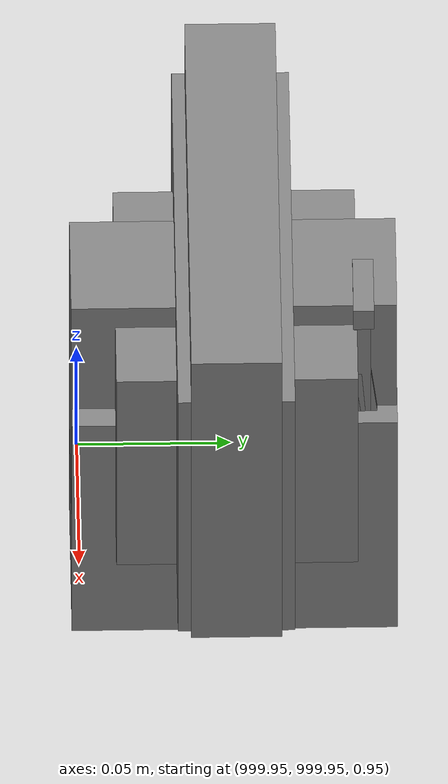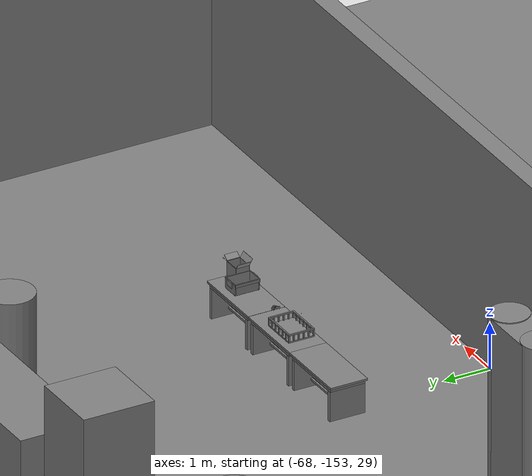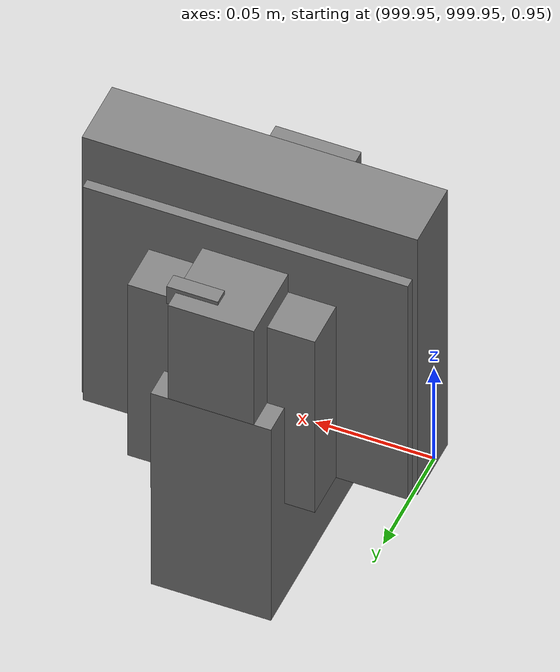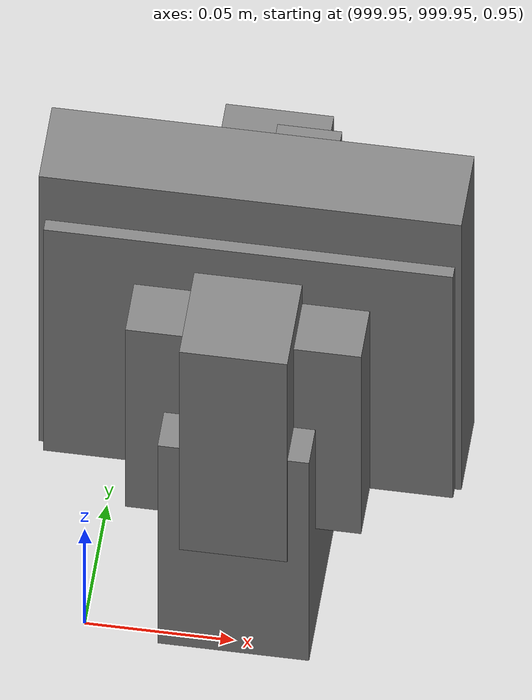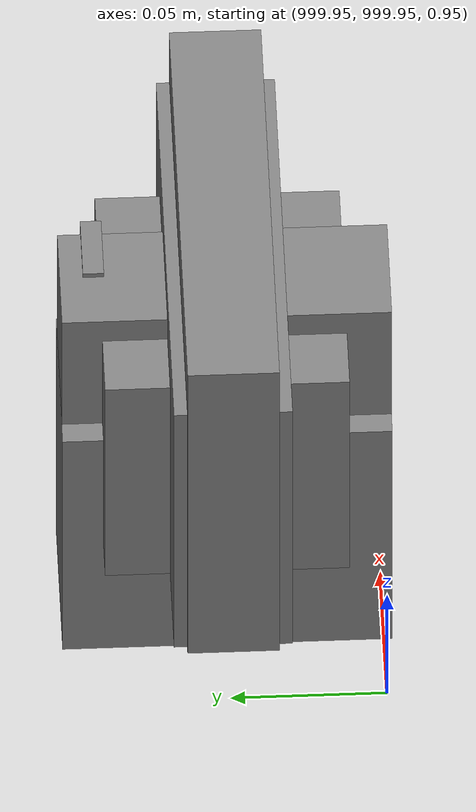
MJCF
<mujoco>
    <option gravity="0.000000000 0.000000000 -9.810000420" timestep="0.0049999999" integrator="implicitfast" density="1.225" viscosity="1.8000001e-05" noslip_iterations="10" iterations="100" sdf_iterations="50">
        <flag multiccd="disable"/>
    </option>
    <size memory="1000M"/>
    <compiler coordinate="local"/>
    <worldbody>
        <light cutoff="30" pos="0 1 1" dir="0 -1 -2"/>
        <light cutoff="30" pos="0 -1 1" dir="0 1 -2"/>
        <body pos="1000.000000000 1000.000000000 1.000000000" euler="0.000000000 0.000000000 180.000000000" name="openloong_gripper_2f85_fix_base_usda_battery_01">
            <geom contype="1" conaffinity="1" density="1000" type="box" material="" rgba="0.500000000 0.500000000 0.500000000 1.000000000" solimp="0.899999976 0.949999988 0.001000000" friction="1.000000000 0.005000000 0.000100000" solref="0.020000000 1.000000000" margin="0" condim="3" group="0" pos="-0.011123657 -0.041940309 0.101691343" quat="1.000000000 0.000000000 0.000000000 0.000000000" size="0.010800000 0.003375000 0.004725000" name="openloong_gripper_2f85_fix_base_usda_geom_2302592B_54C6_4A00_8EDC_C18FA6E62C16"/>
            <geom contype="1" conaffinity="1" density="1000" type="box" material="" rgba="0.500000000 0.500000000 0.500000000 1.000000000" solimp="0.899999976 0.949999988 0.001000000" friction="1.000000000 0.005000000 0.000100000" solref="0.020000000 1.000000000" margin="0" condim="3" group="0" pos="-0.010876465 -0.044247437 0.047066893" quat="0.998702705 -0.050920475 0.000000000 0.000000000" size="0.009450001 0.002700000 0.024975000" name="openloong_gripper_2f85_fix_base_usda_geom_D76DA95E_115A_4529_8DDA_9614267A9E34"/>
            <geom contype="1" conaffinity="1" density="1000" type="box" material="" rgba="0.500000000 0.500000000 0.500000000 1.000000000" solimp="0.899999976 0.949999988 0.001000000" friction="1.000000000 0.005000000 0.000100000" solref="0.020000000 1.000000000" margin="0" condim="3" group="0" pos="-0.001235962 -0.000659180 0.047381196" quat="1.000000000 0.000000000 0.000000000 0.000000000" size="0.039420001 0.039150000 0.047250003" name="openloong_gripper_2f85_fix_base_usda_geom_709382C9_57F8_4B83_A4F3_C679D27DEB66"/>
            <geom contype="1" conaffinity="1" density="1000" type="box" material="" rgba="0.500000000 0.500000000 0.500000000 1.000000000" solimp="0.899999976 0.949999988 0.001000000" friction="1.000000000 0.005000000 0.000100000" solref="0.020000000 1.000000000" margin="0" condim="3" group="0" pos="-0.010876465 -0.039138794 0.009851727" quat="1.000000000 0.000000000 0.000000000 0.000000000" size="0.009450001 0.010800000 0.013500000" name="openloong_gripper_2f85_fix_base_usda_geom_0616763A_4E33_43FF_A0A9_3D9F3E6DD63C"/>
            <geom contype="1" conaffinity="1" density="1000" type="box" material="" rgba="0.500000000 0.500000000 0.500000000 1.000000000" solimp="0.899999976 0.949999988 0.001000000" friction="1.000000000 0.005000000 0.000100000" solref="0.020000000 1.000000000" margin="0" condim="3" group="0" pos="-0.010876465 -0.041528322 0.071508206" quat="1.000000000 0.000000000 0.000000000 0.000000000" size="0.009450001 0.002700000 0.027000001" name="openloong_gripper_2f85_fix_base_usda_geom_A05AE93B_1D8A_4CEB_B6D0_143807AA91EB"/>
            <freejoint name="openloong_gripper_2f85_fix_base_usda_battery_01_joint"/>
            <site size="0.005000000 0.005000000 0.005000000" rgba="0.500000000 0.500000000 0.500000000 1.000000000" pos="0.000000000 0.000000000 0.000000000" quat="0.999961913 0.008726500 0.000000000 0.000000000" group="0" type="sphere" name="openloong_gripper_2f85_fix_base_usda_battery_01site"/>
        </body>
        <body pos="1000.000000000 1000.000000000 1.000000000" euler="0.000000000 0.000000000 180.000000000" name="openloong_gripper_2f85_fix_base_usda_cpu_fan">
            <geom contype="1" conaffinity="1" density="1000" type="box" material="" rgba="0.500000000 0.500000000 0.500000000 1.000000000" solimp="0.899999976 0.949999988 0.001000000" friction="1.000000000 0.005000000 0.000100000" solref="0.020000000 1.000000000" margin="0" condim="3" group="0" pos="0.000000000 0.000000000 0.070034981" quat="0.000000000 0.000000000 0.000000000 1.000000000" size="0.070700005 0.014699999 0.070700005" name="openloong_gripper_2f85_fix_base_usda_geom_D4EC29DE_A871_4D17_AAA9_D73C7327810F"/>
            <freejoint name="openloong_gripper_2f85_fix_base_usda_cpu_fan_joint"/>
            <site size="0.005000000 0.005000000 0.005000000" rgba="0.500000000 0.500000000 0.500000000 1.000000000" pos="0.000000000 0.000000000 0.000000000" quat="0.999961913 0.008726535 0.000000000 0.000000000" group="0" type="sphere" name="openloong_gripper_2f85_fix_base_usda_cpu_fancsite"/>
        </body>
        <body pos="1000.000000000 1000.000000000 1.000000000" euler="0.000000000 0.000000000 180.000000000" name="openloong_gripper_2f85_fix_base_usda_wifi_box">
            <geom contype="1" conaffinity="1" density="1000" type="box" material="" rgba="0.500000000 0.500000000 0.500000000 1.000000000" solimp="0.899999976 0.949999988 0.001000000" friction="1.000000000 0.005000000 0.000100000" solref="0.020000000 1.000000000" margin="0" condim="3" group="0" pos="0.000000000 0.000000000 0.058978677" quat="0.000000000 0.000000047 0.000000000 1.000000000" size="0.068499997 0.018999999 0.059000000" name="openloong_gripper_2f85_fix_base_usda_geom_37D94AB7_5721_4D97_8A76_18240196DD26"/>
            <freejoint name="openloong_gripper_2f85_fix_base_usda_wifi_box_joint"/>
            <site size="0.005000000 0.005000000 0.005000000" rgba="0.500000000 0.500000000 0.500000000 1.000000000" pos="0.000000000 0.000000000 0.000000000" quat="0.999961913 0.008726500 0.000000000 0.000000000" group="0" type="sphere" name="openloong_gripper_2f85_fix_base_usda_wifi_boxsite"/>
        </body>
        <body pos="-66.243659973 -148.895339966 31.170698166" euler="40.370021820 67.000724792 -49.510616302" mocap="true" name="spotlight6_SpotLight"/>
        <body pos="1000.000000000 1000.000000000 1.000000000" euler="0.000011953 0.000005123 -179.999984741" name="openloong_gripper_2f85_fix_base_usda_intel_box">
            <geom contype="1" conaffinity="1" density="1000" type="box" material="" rgba="0.500000000 0.500000000 0.500000000 1.000000000" solimp="0.899999976 0.949999988 0.001000000" friction="1.000000000 0.005000000 0.000100000" solref="0.020000000 1.000000000" margin="0" condim="3" group="0" pos="0.000000000 -0.000067139 0.000082284" quat="0.707106709 0.000000225 0.000000253 0.707106650" size="0.052800003 0.025300000 0.052800003" name="openloong_gripper_2f85_fix_base_usda_geom_D226AB80_2658_4175_B0D9_3FA9542AF78E"/>
            <freejoint name="openloong_gripper_2f85_fix_base_usda_intel_box_joint"/>
            <site size="0.005000000 0.005000000 0.005000000" rgba="0.500000000 0.500000000 0.500000000 1.000000000" pos="0.000000000 0.000000000 0.000000000" quat="0.999961913 0.008726500 0.000000000 0.000000000" group="0" type="sphere" name="openloong_gripper_2f85_fix_base_usda_intel_boxsite"/>
        </body>
        <body pos="1000.000000000 999.999938965 1.000000000" euler="0.000000000 0.000000000 180.000000000" name="openloong_gripper_2f85_fix_base_usda_intelcore_i5">
            <geom contype="1" conaffinity="1" density="1000" type="box" material="" rgba="0.500000000 0.500000000 0.500000000 1.000000000" solimp="0.899999976 0.949999988 0.001000000" friction="1.000000000 0.005000000 0.000100000" solref="0.020000000 1.000000000" margin="0" condim="3" group="0" pos="0.000000000 0.000000000 0.051722717" quat="0.707106709 0.000000000 0.000000000 -0.707106769" size="0.052800000 0.018080002 0.052800000" name="openloong_gripper_2f85_fix_base_usda_geom_047F6CC4_118D_44F5_B8AF_07BA990CA56F"/>
            <freejoint name="openloong_gripper_2f85_fix_base_usda_intelcore_i5_joint"/>
            <site size="0.005000000 0.005000000 0.005000000" rgba="0.500000000 0.500000000 0.500000000 1.000000000" pos="0.000000000 0.000000000 0.000000000" quat="0.999961913 0.008726534 0.000000000 0.000000000" group="0" type="sphere" name="openloong_gripper_2f85_fix_base_usda_intelcore_i5site"/>
        </body>
        <body pos="-66.240776062 -149.298019409 31.166408539" euler="-155.641479492 -14.758358002 12.705614090" mocap="true" name="spotlight1_SpotLight"/>
        <body pos="-66.086875916 -149.216125488 31.168415070" euler="-174.497238159 82.377517700 -167.432891846" mocap="true" name="spotlight4_SpotLight"/>
        <body pos="-64.866622925 -149.383972168 30.183746338" euler="89.999984741 89.999946594 0.000000000" name="openloong_gripper_2f85_fix_base_usda_bluebox_01">
            <geom contype="1" conaffinity="1" density="1000" type="box" material="" rgba="0.500000000 0.500000000 0.500000000 1.000000000" solimp="0.899999976 0.949999988 0.001000000" friction="1.000000000 0.005000000 0.000100000" solref="0.020000000 1.000000000" margin="0" condim="3" group="0" pos="0.276580811 0.187225342 0.000068665" quat="0.707106948 0.000077471 0.707106352 0.000077486" size="0.100000001 0.057999998 0.010000000" name="openloong_gripper_2f85_fix_base_usda_geom_43F82F9B_E3C6_4055_906F_EBC25560F01B"/>
            <geom contype="1" conaffinity="1" density="1000" type="box" material="" rgba="0.500000000 0.500000000 0.500000000 1.000000000" solimp="0.899999976 0.949999988 0.001000000" friction="1.000000000 0.005000000 0.000100000" solref="0.020000000 1.000000000" margin="0" condim="3" group="0" pos="0.000000000 0.002883911 0.000000000" quat="0.999999881 0.000000000 0.000000000 0.000000000" size="0.254000008 0.003000000 0.172000006" name="openloong_gripper_2f85_fix_base_usda_geom_1DC4C24A_81EB_431F_BAD3_DFE51F2F928A"/>
            <geom contype="1" conaffinity="1" density="1000" type="box" material="" rgba="0.500000000 0.500000000 0.500000000 1.000000000" solimp="0.899999976 0.949999988 0.001000000" friction="1.000000000 0.005000000 0.000100000" solref="0.020000000 1.000000000" margin="0" condim="3" group="0" pos="0.000000000 0.124874115 0.173484802" quat="0.999796331 0.020176515 -0.000000015 0.000000030" size="0.259999990 0.119999997 0.007000000" name="openloong_gripper_2f85_fix_base_usda_geom_6371C742_DC87_4FDF_B5D9_F60175DD5131"/>
            <geom contype="1" conaffinity="1" density="1000" type="box" material="" rgba="0.500000000 0.500000000 0.500000000 1.000000000" solimp="0.899999976 0.949999988 0.001000000" friction="1.000000000 0.005000000 0.000100000" solref="0.020000000 1.000000000" margin="0" condim="3" group="0" pos="0.000000000 0.124874115 -0.173469543" quat="0.999796331 -0.020176545 -0.000000015 0.000000000" size="0.259999990 0.119999997 0.007000000" name="openloong_gripper_2f85_fix_base_usda_geom_17FCFAA6_62A2_4FDE_A3EE_FBCD02BCF7DE"/>
            <geom contype="1" conaffinity="1" density="1000" type="box" material="" rgba="0.500000000 0.500000000 0.500000000 1.000000000" solimp="0.899999976 0.949999988 0.001000000" friction="1.000000000 0.005000000 0.000100000" solref="0.020000000 1.000000000" margin="0" condim="3" group="0" pos="0.000000000 0.214008331 0.188980103" quat="0.999912977 0.013176724 0.000000015 0.000000000" size="0.259999990 0.029999999 0.012500000" name="openloong_gripper_2f85_fix_base_usda_geom_549B1D03_0CB2_4954_9695_40FFD0517192"/>
            <geom contype="1" conaffinity="1" density="1000" type="box" material="" rgba="0.500000000 0.500000000 0.500000000 1.000000000" solimp="0.899999976 0.949999988 0.001000000" friction="1.000000000 0.005000000 0.000100000" solref="0.020000000 1.000000000" margin="0" condim="3" group="0" pos="-0.258361816 0.125289917 0.001876831" quat="0.702796936 -0.020792112 0.710783124 0.020769298" size="0.189999998 0.119999997 0.009000000" name="openloong_gripper_2f85_fix_base_usda_geom_8E51B500_D4AA_463F_8E13_00E0DC2EF9D7"/>
            <geom contype="1" conaffinity="1" density="1000" type="box" material="" rgba="0.500000000 0.500000000 0.500000000 1.000000000" solimp="0.899999976 0.949999988 0.001000000" friction="1.000000000 0.005000000 0.000100000" solref="0.020000000 1.000000000" margin="0" condim="3" group="0" pos="0.000000000 0.214008331 -0.188980103" quat="0.999912977 -0.013176769 0.000000030 0.000000015" size="0.259999990 0.029999999 0.012500000" name="openloong_gripper_2f85_fix_base_usda_geom_0120E3D4_A118_4258_AD6B_E00A9E454EAF"/>
            <geom contype="1" conaffinity="1" density="1000" type="box" material="" rgba="0.500000000 0.500000000 0.500000000 1.000000000" solimp="0.899999976 0.949999988 0.001000000" friction="1.000000000 0.005000000 0.000100000" solref="0.020000000 1.000000000" margin="0" condim="3" group="0" pos="-0.276611328 0.187225342 0.000068665" quat="0.707106650 0.000077441 0.707106709 0.000077456" size="0.100000001 0.057999998 0.010000000" name="openloong_gripper_2f85_fix_base_usda_geom_FAD6EE1B_AE10_4420_8C01_014C6330A4C2"/>
            <geom contype="1" conaffinity="1" density="1000" type="box" material="" rgba="0.500000000 0.500000000 0.500000000 1.000000000" solimp="0.899999976 0.949999988 0.001000000" friction="1.000000000 0.005000000 0.000100000" solref="0.020000000 1.000000000" margin="0" condim="3" group="0" pos="0.258331299 0.125289917 0.001876831" quat="0.702851415 0.018856421 0.710823774 -0.019329369" size="0.189999998 0.119999997 0.009000000" name="openloong_gripper_2f85_fix_base_usda_geom_5D2EE3F8_9D7C_4701_B094_7A7BEA94FA18"/>
            <freejoint name="openloong_gripper_2f85_fix_base_usda_bluebox_01_joint"/>
            <site size="0.005000000 0.005000000 0.005000000" rgba="0.500000000 0.500000000 0.500000000 1.000000000" pos="0.000000000 0.000000000 0.000000000" quat="0.999961913 0.008726534 0.000000000 0.000000000" group="0" type="sphere" name="openloong_gripper_2f85_fix_base_usda_bluebox_01site"/>
        </body>
        <body pos="-64.496299744 -149.491867065 30.235729218" euler="0.000000000 0.000000000 89.999946594" name="openloong_gripper_2f85_fix_base_usda_cardboardbox_01">
            <geom contype="1" conaffinity="1" density="1000" type="box" material="" rgba="0.500000000 0.500000000 0.500000000 1.000000000" solimp="0.899999976 0.949999988 0.001000000" friction="1.000000000 0.005000000 0.000100000" solref="0.020000000 1.000000000" margin="0" condim="3" group="0" pos="-0.003166199 -0.004086494 0.005052090" quat="1.000000000 0.000000000 0.000000000 0.000000000" size="0.142499998 0.177500010 0.005000000" name="openloong_gripper_2f85_fix_base_usda_geom_1520F7E8_3401_4B6B_9D27_37F2A0348214"/>
            <geom contype="1" conaffinity="1" density="1000" type="box" material="" rgba="0.500000000 0.500000000 0.500000000 1.000000000" solimp="0.899999976 0.949999988 0.001000000" friction="1.000000000 0.005000000 0.000100000" solref="0.020000000 1.000000000" margin="0" condim="3" group="0" pos="-0.003166199 0.170316696 0.150570869" quat="1.000000000 0.000000000 0.000000000 0.000000000" size="0.142499998 0.005000000 0.149999991" name="openloong_gripper_2f85_fix_base_usda_geom_6B13299C_BB8F_4A92_A847_D74694311C7A"/>
            <geom contype="1" conaffinity="1" density="1000" type="box" material="" rgba="0.500000000 0.500000000 0.500000000 1.000000000" solimp="0.899999976 0.949999988 0.001000000" friction="1.000000000 0.005000000 0.000100000" solref="0.020000000 1.000000000" margin="0" condim="3" group="0" pos="-0.147399902 -0.005307198 0.150570869" quat="1.000000000 0.000000000 0.000000000 0.000000000" size="0.005000000 0.177500010 0.149999991" name="openloong_gripper_2f85_fix_base_usda_geom_5D4DAAEC_46B0_47C4_8DAA_5EFD2C5E5919"/>
            <geom contype="1" conaffinity="1" density="1000" type="box" material="" rgba="0.500000000 0.500000000 0.500000000 1.000000000" solimp="0.899999976 0.949999988 0.001000000" friction="1.000000000 0.005000000 0.000100000" solref="0.020000000 1.000000000" margin="0" condim="3" group="0" pos="0.140275955 -0.005307198 0.150570869" quat="1.000000000 0.000000000 0.000000000 0.000000000" size="0.005000000 0.177500010 0.149999991" name="openloong_gripper_2f85_fix_base_usda_geom_B0F69BA4_5948_4CD7_B36E_85E5ECB2434B"/>
            <geom contype="1" conaffinity="1" density="1000" type="box" material="" rgba="0.500000000 0.500000000 0.500000000 1.000000000" solimp="0.899999976 0.949999988 0.001000000" friction="1.000000000 0.005000000 0.000100000" solref="0.020000000 1.000000000" margin="0" condim="3" group="0" pos="-0.003166199 -0.181550980 0.150570869" quat="1.000000000 0.000000000 0.000000000 0.000000000" size="0.142499998 0.005000000 0.149999991" name="openloong_gripper_2f85_fix_base_usda_geom_0A9193E6_FF21_4516_946E_D607B90F59D7"/>
            <freejoint name="openloong_gripper_2f85_fix_base_usda_cardboardbox_01_joint"/>
            <site size="0.005000000 0.005000000 0.005000000" rgba="0.500000000 0.500000000 0.500000000 1.000000000" pos="0.000000000 0.000000000 0.000000000" quat="0.999961913 0.008726535 0.000000000 0.000000000" group="0" type="sphere" name="openloong_gripper_2f85_fix_base_usda_site_76CF54D7_0ABA_4115_BC71_7577B6A9DFF5"/>
            <body pos="0.139160156 -0.004048347 0.301930904" euler="-179.999954224 49.383502960 179.999954224" name="openloong_gripper_2f85_fix_base_usda_A1_006">
                <geom contype="1" conaffinity="1" density="1000" type="box" material="" rgba="0.500000000 0.500000000 0.500000000 1.000000000" solimp="0.899999976 0.949999988 0.001000000" friction="1.000000000 0.005000000 0.000100000" solref="0.020000000 1.000000000" margin="0" condim="3" group="0" pos="-0.071587563 0.000009537 0.001745224" quat="0.999999881 0.000000000 0.000000000 0.000000000" size="0.071249999 0.179999992 0.002500000" name="openloong_gripper_2f85_fix_base_usda_geom_6F6498FB_BB20_4518_8586_7C493B9B75A3"/>
                <joint armature="0" stiffness="0.07" damping="0.0099999998" axis="0.000000 1.000000 0.000000" type="hinge" name="openloong_gripper_2f85_fix_base_usda_A1_006"/>
            </body>
            <body pos="-0.145902634 -0.004086494 0.301938057" euler="-180.000000000 -60.000011444 -180.000000000" name="openloong_gripper_2f85_fix_base_usda_A2_006">
                <geom contype="1" conaffinity="1" density="1000" type="box" material="" rgba="0.500000000 0.500000000 0.500000000 1.000000000" solimp="0.899999976 0.949999988 0.001000000" friction="1.000000000 0.005000000 0.000100000" solref="0.020000000 1.000000000" margin="0" condim="3" group="0" pos="0.071268082 0.000009537 0.002717972" quat="0.000002921 0.000000000 -0.000000030 0.999999881" size="0.071249999 0.179999992 0.002500000" name="openloong_gripper_2f85_fix_base_usda_geom_D22C5E76_5068_4B30_A193_26E363EFDBC5"/>
                <joint armature="0" stiffness="0.07" damping="0.0099999998" axis="0.000000 1.000000 0.000000" type="hinge" name="openloong_gripper_2f85_fix_base_usda_A2_006"/>
            </body>
            <body pos="-0.003385544 0.175991058 0.301930904" euler="-125.858116150 -0.000004561 0.000002331" name="openloong_gripper_2f85_fix_base_usda_B2_006">
                <geom contype="1" conaffinity="1" density="1000" type="box" material="" rgba="0.500000000 0.500000000 0.500000000 1.000000000" solimp="0.899999976 0.949999988 0.001000000" friction="1.000000000 0.005000000 0.000100000" solref="0.020000000 1.000000000" margin="0" condim="3" group="0" pos="0.000009537 -0.070939064 -0.002470016" quat="0.999614120 0.027776197 -0.000000015 0.000000030" size="0.137500003 0.064999998 0.005000000" name="openloong_gripper_2f85_fix_base_usda_geom_C33DC85F_8423_4425_879C_AF8C3D2298BF"/>
                <joint armature="0" stiffness="0.07" damping="0.0099999998" axis="1.000000 0.000000 0.000000" type="hinge" name="openloong_gripper_2f85_fix_base_usda_B2_006"/>
            </body>
            <body pos="-0.003385544 -0.184140205 0.301938057" euler="147.805557251 0.000000000 0.000000000" name="openloong_gripper_2f85_fix_base_usda_B1_006">
                <geom contype="1" conaffinity="1" density="1000" type="box" material="" rgba="0.500000000 0.500000000 0.500000000 1.000000000" solimp="0.899999976 0.949999988 0.001000000" friction="1.000000000 0.005000000 0.000100000" solref="0.020000000 1.000000000" margin="0" condim="3" group="0" pos="-0.000028610 0.070202351 -0.002703667" quat="0.999614179 -0.027776167 0.000000000 0.000000000" size="0.137500003 0.064999998 0.005000000" name="openloong_gripper_2f85_fix_base_usda_geom_3A662356_A007_43AE_9687_8ACCD14A9283"/>
                <joint armature="0" stiffness="0.07" damping="0.0099999998" axis="1.000000 0.000000 0.000000" type="hinge" name="openloong_gripper_2f85_fix_base_usda_B1_006"/>
            </body>
        </body>
        <body pos="-65.882858276 -149.481979370 30.229999542" euler="-64.487716675 0.000000000 0.000000000" name="openloong_gripper_2f85_fix_base_usda_Barcode">
            <geom contype="1" conaffinity="1" density="1000" type="box" material="" rgba="0.500000000 0.500000000 0.500000000 1.000000000" solimp="0.899999976 0.949999988 0.001000000" friction="1.000000000 0.005000000 0.000100000" solref="0.020000000 1.000000000" margin="0" condim="3" group="0" pos="0.000000000 0.013038635 0.001419067" quat="0.000000000 0.000000000 0.000000000 1.000000119" size="0.034000002 0.010000000 0.017999999" name="openloong_gripper_2f85_fix_base_usda_geom_578BE187_8D3B_40EA_A891_475C0D7717A7"/>
            <geom contype="1" conaffinity="1" density="1000" type="box" material="" rgba="0.500000000 0.500000000 0.500000000 1.000000000" solimp="0.899999976 0.949999988 0.001000000" friction="1.000000000 0.005000000 0.000100000" solref="0.020000000 1.000000000" margin="0" condim="3" group="0" pos="0.000000000 -0.035301208 -0.007095337" quat="0.000000000 0.000000000 -0.043619365 0.999048233" size="0.028999999 0.010000000 0.020000000" name="openloong_gripper_2f85_fix_base_usda_geom_69AA11E8_5A40_476E_8008_F962C56D6CC6"/>
            <geom contype="1" conaffinity="1" density="1000" type="box" material="" rgba="0.500000000 0.500000000 0.500000000 1.000000000" solimp="0.899999976 0.949999988 0.001000000" friction="1.000000000 0.005000000 0.000100000" solref="0.020000000 1.000000000" margin="0" condim="3" group="0" pos="0.000000000 -0.043411255 -0.011749268" quat="0.922262907 0.386563420 0.000000000 0.000000000" size="0.026000001 0.010000000 0.020000000" name="openloong_gripper_2f85_fix_base_usda_geom_E1C3D36E_77E4_46A9_B4B2_DECA3082CE0A"/>
            <geom contype="1" conaffinity="1" density="1000" type="box" material="" rgba="0.500000000 0.500000000 0.500000000 1.000000000" solimp="0.899999976 0.949999988 0.001000000" friction="1.000000000 0.005000000 0.000100000" solref="0.020000000 1.000000000" margin="0" condim="3" group="0" pos="0.000000000 -0.016967773 -0.031860352" quat="0.000000000 0.000000000 0.000000000 1.000000119" size="0.008000000 0.010000000 0.013000000" name="openloong_gripper_2f85_fix_base_usda_geom_D2DF4DD2_38CE_4A82_B287_09FC6BD8A05F"/>
            <geom contype="1" conaffinity="1" density="1000" type="box" material="" rgba="0.500000000 0.500000000 0.500000000 1.000000000" solimp="0.899999976 0.949999988 0.001000000" friction="1.000000000 0.005000000 0.000100000" solref="0.020000000 1.000000000" margin="0" condim="3" group="0" pos="0.000000000 -0.001869202 0.000312805" quat="0.953716993 0.300705761 0.000000000 0.000000000" size="0.032000002 0.010000000 0.018999999" name="openloong_gripper_2f85_fix_base_usda_geom_D3CC989C_E20E_4DE0_AC36_DCE8375EB6FC"/>
            <geom contype="1" conaffinity="1" density="1000" type="box" material="" rgba="0.500000000 0.500000000 0.500000000 1.000000000" solimp="0.899999976 0.949999988 0.001000000" friction="1.000000000 0.005000000 0.000100000" solref="0.020000000 1.000000000" margin="0" condim="3" group="0" pos="0.000000000 -0.019531250 -0.003173828" quat="0.953716993 0.300705761 0.000000000 0.000000000" size="0.030999999 0.010000000 0.020000000" name="openloong_gripper_2f85_fix_base_usda_geom_4063CCCC_6B2C_42C4_AFB9_DFDA3A84FE0D"/>
            <geom contype="1" conaffinity="1" density="1000" type="box" material="" rgba="0.500000000 0.500000000 0.500000000 1.000000000" solimp="0.899999976 0.949999988 0.001000000" friction="1.000000000 0.005000000 0.000100000" solref="0.020000000 1.000000000" margin="0" condim="3" group="0" pos="0.000000000 -0.035301208 -0.007095337" quat="0.953716993 0.300705761 0.000000000 0.000000000" size="0.028999999 0.010000000 0.020000000" name="openloong_gripper_2f85_fix_base_usda_geom_7D1328A9_0077_4462_9E46_B8A4883A35BE"/>
            <geom contype="1" conaffinity="1" density="1000" type="box" material="" rgba="0.500000000 0.500000000 0.500000000 1.000000000" solimp="0.899999976 0.949999988 0.001000000" friction="1.000000000 0.005000000 0.000100000" solref="0.020000000 1.000000000" margin="0" condim="3" group="0" pos="0.000000000 -0.042617798 -0.071121216" quat="0.000000000 0.000000000 0.000000000 1.000000119" size="0.013000000 0.021000000 0.059999999" name="openloong_gripper_2f85_fix_base_usda_geom_DC338508_8CD8_4141_B6F2_02A566DFEF99"/>
            <freejoint name="openloong_gripper_2f85_fix_base_usda_Barcode_joint"/>
            <site size="0.005000000 0.005000000 0.005000000" rgba="0.500000000 0.500000000 0.500000000 1.000000000" pos="0.000000000 0.000000000 0.000000000" quat="1.000000000 0.000000000 0.000000000 0.000000000" group="0" type="sphere" name="openloong_gripper_2f85_fix_base_usda_Barcode_site"/>
        </body>
        <body pos="-66.745018005 -149.392349243 30.184000015" euler="0.000000000 0.000000000 89.999946594" name="[22333343301294]_Basket_01">
            <geom contype="1" conaffinity="1" density="1000" type="box" material="" rgba="0.500000000 0.500000000 0.500000000 1.000000000" solimp="0.899999976 0.949999988 0.001000000" friction="1.000000000 0.005000000 0.000100000" solref="0.020000000 1.000000000" margin="0" condim="3" group="0" pos="-0.052425385 0.389207840 0.089787483" quat="0.707107008 0.000000000 0.000000000 0.707106411" size="0.014249999 0.014249999 0.059999999" name="[22333343301294]_geom_4D82BDF6_E6C7_4962_86FF_3427223D90DB"/>
            <geom contype="1" conaffinity="1" density="1000" type="box" material="" rgba="0.500000000 0.500000000 0.500000000 1.000000000" solimp="0.899999976 0.949999988 0.001000000" friction="1.000000000 0.005000000 0.000100000" solref="0.020000000 1.000000000" margin="0" condim="3" group="0" pos="0.264015198 -0.133043289 0.089787483" quat="0.707107008 0.000000000 0.000000000 0.707106411" size="0.014249999 0.014249999 0.059999999" name="[22333343301294]_geom_72A34C16_58AB_4C06_BC2A_9B3D7336FEAA"/>
            <geom contype="1" conaffinity="1" density="1000" type="box" material="" rgba="0.500000000 0.500000000 0.500000000 1.000000000" solimp="0.899999976 0.949999988 0.001000000" friction="1.000000000 0.005000000 0.000100000" solref="0.020000000 1.000000000" margin="0" condim="3" group="0" pos="-0.264015198 -0.265548706 0.089793205" quat="0.707107008 0.000000000 0.000000000 0.707106411" size="0.014249999 0.014249999 0.059999999" name="[22333343301294]_geom_C3E372D5_8DD6_4799_B7DE_86771E8BECFB"/>
            <geom contype="1" conaffinity="1" density="1000" type="box" material="" rgba="0.500000000 0.500000000 0.500000000 1.000000000" solimp="0.899999976 0.949999988 0.001000000" friction="1.000000000 0.005000000 0.000100000" solref="0.020000000 1.000000000" margin="0" condim="3" group="0" pos="-0.160263062 -0.389322281 0.089793205" quat="0.707107008 0.000000000 0.000000000 0.707106411" size="0.014249999 0.014249999 0.059999999" name="[22333343301294]_geom_0380F102_B937_49DD_ABA6_CAFDFE1EF647"/>
            <geom contype="1" conaffinity="1" density="1000" type="box" material="" rgba="0.500000000 0.500000000 0.500000000 1.000000000" solimp="0.899999976 0.949999988 0.001000000" friction="1.000000000 0.005000000 0.000100000" solref="0.020000000 1.000000000" margin="0" condim="3" group="0" pos="0.162265778 -0.389322281 0.089787483" quat="0.707107008 0.000000000 0.000000000 0.707106411" size="0.014249999 0.014249999 0.059999999" name="[22333343301294]_geom_B7124180_41BD_4000_9EFD_B565D3E90D64"/>
            <geom contype="1" conaffinity="1" density="1000" type="box" material="" rgba="0.500000000 0.500000000 0.500000000 1.000000000" solimp="0.899999976 0.949999988 0.001000000" friction="1.000000000 0.005000000 0.000100000" solref="0.020000000 1.000000000" margin="0" condim="3" group="0" pos="0.264015198 0.389207840 0.089787483" quat="0.707107008 0.000000000 0.000000000 0.707106411" size="0.014249999 0.014249999 0.059999999" name="[22333343301294]_geom_93B92628_3593_4790_904A_FC476304AEA6"/>
            <geom contype="1" conaffinity="1" density="1000" type="box" material="" rgba="0.500000000 0.500000000 0.500000000 1.000000000" solimp="0.899999976 0.949999988 0.001000000" friction="1.000000000 0.005000000 0.000100000" solref="0.020000000 1.000000000" margin="0" condim="3" group="0" pos="-0.264015198 -0.133043289 0.089793205" quat="0.707107008 0.000000000 0.000000000 0.707106411" size="0.014249999 0.014249999 0.059999999" name="[22333343301294]_geom_C08F0353_1174_4855_A876_1064749368BB"/>
            <geom contype="1" conaffinity="1" density="1000" type="box" material="" rgba="0.500000000 0.500000000 0.500000000 1.000000000" solimp="0.899999976 0.949999988 0.001000000" friction="1.000000000 0.005000000 0.000100000" solref="0.020000000 1.000000000" margin="0" condim="3" group="0" pos="-0.264026642 0.269256592 0.089793205" quat="0.707107008 0.000000000 0.000000000 0.707106411" size="0.014249999 0.014249999 0.059999999" name="[22333343301294]_geom_FB8FC438_CAFC_4688_98D0_B79DE42EDD02"/>
            <geom contype="1" conaffinity="1" density="1000" type="box" material="" rgba="0.500000000 0.500000000 0.500000000 1.000000000" solimp="0.899999976 0.949999988 0.001000000" friction="1.000000000 0.005000000 0.000100000" solref="0.020000000 1.000000000" margin="0" condim="3" group="0" pos="0.054462433 0.389207840 0.089787483" quat="0.707107008 0.000000000 0.000000000 0.707106411" size="0.014249999 0.014249999 0.059999999" name="[22333343301294]_geom_21BA96EB_F786_4E1A_81F8_AECF90B9F4E3"/>
            <geom contype="1" conaffinity="1" density="1000" type="box" material="" rgba="0.500000000 0.500000000 0.500000000 1.000000000" solimp="0.899999976 0.949999988 0.001000000" friction="1.000000000 0.005000000 0.000100000" solref="0.020000000 1.000000000" margin="0" condim="3" group="0" pos="0.054462433 -0.389322281 0.089787483" quat="0.707107008 0.000000000 0.000000000 0.707106411" size="0.014249999 0.014249999 0.059999999" name="[22333343301294]_geom_F19859C4_215F_4ABE_9C10_E6111FC5FA55"/>
            <geom contype="1" conaffinity="1" density="1000" type="box" material="" rgba="0.500000000 0.500000000 0.500000000 1.000000000" solimp="0.899999976 0.949999988 0.001000000" friction="1.000000000 0.005000000 0.000100000" solref="0.020000000 1.000000000" margin="0" condim="3" group="0" pos="0.264015198 0.269256592 0.089793205" quat="0.707107008 0.000000000 0.000000000 0.707106411" size="0.014249999 0.014249999 0.059999999" name="[22333343301294]_geom_8EEA9F8D_25A1_4AFD_B195_CF2B05D63F12"/>
            <geom contype="1" conaffinity="1" density="1000" type="box" material="" rgba="0.500000000 0.500000000 0.500000000 1.000000000" solimp="0.899999976 0.949999988 0.001000000" friction="1.000000000 0.005000000 0.000100000" solref="0.020000000 1.000000000" margin="0" condim="3" group="0" pos="0.264015198 -0.389322281 0.089787483" quat="0.707107008 0.000000000 0.000000000 0.707106411" size="0.014249999 0.014249999 0.059999999" name="[22333343301294]_geom_CC62D794_2AFD_4994_96BD_1ACC7C1458F5"/>
            <geom contype="1" conaffinity="1" density="1000" type="box" material="" rgba="0.500000000 0.500000000 0.500000000 1.000000000" solimp="0.899999976 0.949999988 0.001000000" friction="1.000000000 0.005000000 0.000100000" solref="0.020000000 1.000000000" margin="0" condim="3" group="0" pos="0.000000000 0.000000000 0.015998840" quat="0.707107008 0.000000000 0.000000000 0.707106411" size="0.403499991 0.279000014 0.015750000" name="[22333343301294]_geom_4A9B9127_4C6F_4996_A9E6_0A7B8ABA1FFF"/>
            <geom contype="1" conaffinity="1" density="1000" type="box" material="" rgba="0.500000000 0.500000000 0.500000000 1.000000000" solimp="0.899999976 0.949999988 0.001000000" friction="1.000000000 0.005000000 0.000100000" solref="0.020000000 1.000000000" margin="0" condim="3" group="0" pos="0.000000000 -0.389476776 0.163619041" quat="0.707107008 0.000000000 0.000000000 0.707106411" size="0.015000000 0.277500004 0.015750000" name="[22333343301294]_geom_C7E4ED25_4372_4479_888E_8634D5A92862"/>
            <geom contype="1" conaffinity="1" density="1000" type="box" material="" rgba="0.500000000 0.500000000 0.500000000 1.000000000" solimp="0.899999976 0.949999988 0.001000000" friction="1.000000000 0.005000000 0.000100000" solref="0.020000000 1.000000000" margin="0" condim="3" group="0" pos="0.162265778 0.389207840 0.089787483" quat="0.707107008 0.000000000 0.000000000 0.707106411" size="0.014249999 0.014249999 0.059999999" name="[22333343301294]_geom_FB3CA3E9_3454_4782_933F_8856B5CABB5A"/>
            <geom contype="1" conaffinity="1" density="1000" type="box" material="" rgba="0.500000000 0.500000000 0.500000000 1.000000000" solimp="0.899999976 0.949999988 0.001000000" friction="1.000000000 0.005000000 0.000100000" solref="0.020000000 1.000000000" margin="0" condim="3" group="0" pos="0.000000000 0.389471054 0.163619041" quat="0.707107008 0.000000000 0.000000000 0.707106411" size="0.015000000 0.277500004 0.015750000" name="[22333343301294]_geom_0834CCB2_1A9C_48AF_8788_482AB731ECEC"/>
            <geom contype="1" conaffinity="1" density="1000" type="box" material="" rgba="0.500000000 0.500000000 0.500000000 1.000000000" solimp="0.899999976 0.949999988 0.001000000" friction="1.000000000 0.005000000 0.000100000" solref="0.020000000 1.000000000" margin="0" condim="3" group="0" pos="-0.263511658 0.000000000 0.163619041" quat="0.707107008 0.000000000 0.000000000 0.707106411" size="0.403499991 0.015000000 0.015750000" name="[22333343301294]_geom_69C59046_D78F_4CE9_8A1B_38351B4CCD66"/>
            <geom contype="1" conaffinity="1" density="1000" type="box" material="" rgba="0.500000000 0.500000000 0.500000000 1.000000000" solimp="0.899999976 0.949999988 0.001000000" friction="1.000000000 0.005000000 0.000100000" solref="0.020000000 1.000000000" margin="0" condim="3" group="0" pos="-0.264015198 0.141334534 0.089793205" quat="0.707107008 0.000000000 0.000000000 0.707106411" size="0.014249999 0.014249999 0.059999999" name="[22333343301294]_geom_22599A95_0A96_4EE1_9237_387EAE90B95E"/>
            <geom contype="1" conaffinity="1" density="1000" type="box" material="" rgba="0.500000000 0.500000000 0.500000000 1.000000000" solimp="0.899999976 0.949999988 0.001000000" friction="1.000000000 0.005000000 0.000100000" solref="0.020000000 1.000000000" margin="0" condim="3" group="0" pos="0.264015198 -0.265548706 0.089787483" quat="0.707107008 0.000000000 0.000000000 0.707106411" size="0.014249999 0.014249999 0.059999999" name="[22333343301294]_geom_CA2BAF38_3283_4692_8252_151143CD3227"/>
            <geom contype="1" conaffinity="1" density="1000" type="box" material="" rgba="0.500000000 0.500000000 0.500000000 1.000000000" solimp="0.899999976 0.949999988 0.001000000" friction="1.000000000 0.005000000 0.000100000" solref="0.020000000 1.000000000" margin="0" condim="3" group="0" pos="-0.160263062 0.389207840 0.089787483" quat="0.707107008 0.000000000 0.000000000 0.707106411" size="0.014249999 0.014249999 0.059999999" name="[22333343301294]_geom_D72336EF_B13F_4579_B426_8821F9344545"/>
            <geom contype="1" conaffinity="1" density="1000" type="box" material="" rgba="0.500000000 0.500000000 0.500000000 1.000000000" solimp="0.899999976 0.949999988 0.001000000" friction="1.000000000 0.005000000 0.000100000" solref="0.020000000 1.000000000" margin="0" condim="3" group="0" pos="-0.052425385 -0.389322281 0.089787483" quat="0.707107008 0.000000000 0.000000000 0.707106411" size="0.014249999 0.014249999 0.059999999" name="[22333343301294]_geom_4514155E_1C84_4833_B87C_AD445BE85F51"/>
            <geom contype="1" conaffinity="1" density="1000" type="box" material="" rgba="0.500000000 0.500000000 0.500000000 1.000000000" solimp="0.899999976 0.949999988 0.001000000" friction="1.000000000 0.005000000 0.000100000" solref="0.020000000 1.000000000" margin="0" condim="3" group="0" pos="-0.264026642 -0.389322281 0.089793205" quat="0.707107008 0.000000000 0.000000000 0.707106411" size="0.014249999 0.014249999 0.059999999" name="[22333343301294]_geom_73F12C16_2B59_4E67_8E9F_E19020F54392"/>
            <geom contype="1" conaffinity="1" density="1000" type="box" material="" rgba="0.500000000 0.500000000 0.500000000 1.000000000" solimp="0.899999976 0.949999988 0.001000000" friction="1.000000000 0.005000000 0.000100000" solref="0.020000000 1.000000000" margin="0" condim="3" group="0" pos="0.264015198 0.141334534 0.089787483" quat="0.707107008 0.000000000 0.000000000 0.707106411" size="0.014249999 0.014249999 0.059999999" name="[22333343301294]_geom_A08DC180_D439_42E8_AE9E_F96F6CEB6E99"/>
            <geom contype="1" conaffinity="1" density="1000" type="box" material="" rgba="0.500000000 0.500000000 0.500000000 1.000000000" solimp="0.899999976 0.949999988 0.001000000" friction="1.000000000 0.005000000 0.000100000" solref="0.020000000 1.000000000" margin="0" condim="3" group="0" pos="-0.264015198 0.389207840 0.089793205" quat="0.707107008 0.000000000 0.000000000 0.707106411" size="0.014249999 0.014249999 0.059999999" name="[22333343301294]_geom_4936205E_826D_4F4C_A001_A7322E3E17B1"/>
            <geom contype="1" conaffinity="1" density="1000" type="box" material="" rgba="0.500000000 0.500000000 0.500000000 1.000000000" solimp="0.899999976 0.949999988 0.001000000" friction="1.000000000 0.005000000 0.000100000" solref="0.020000000 1.000000000" margin="0" condim="3" group="0" pos="0.264015198 0.004480362 0.089787483" quat="0.707107008 0.000000000 0.000000000 0.707106411" size="0.014249999 0.014249999 0.059999999" name="[22333343301294]_geom_AE794AAF_A954_41FD_ACB8_60297670ECAC"/>
            <geom contype="1" conaffinity="1" density="1000" type="box" material="" rgba="0.500000000 0.500000000 0.500000000 1.000000000" solimp="0.899999976 0.949999988 0.001000000" friction="1.000000000 0.005000000 0.000100000" solref="0.020000000 1.000000000" margin="0" condim="3" group="0" pos="0.263694763 -0.000011444 0.163619041" quat="0.707107008 0.000000000 0.000000000 0.707106411" size="0.403499991 0.015000000 0.015750000" name="[22333343301294]_geom_D1007189_77D3_48CE_B231_5E0870889386"/>
            <geom contype="1" conaffinity="1" density="1000" type="box" material="" rgba="0.500000000 0.500000000 0.500000000 1.000000000" solimp="0.899999976 0.949999988 0.001000000" friction="1.000000000 0.005000000 0.000100000" solref="0.020000000 1.000000000" margin="0" condim="3" group="0" pos="-0.264015198 0.004480362 0.089793205" quat="0.707107008 0.000000000 0.000000000 0.707106411" size="0.014249999 0.014249999 0.059999999" name="[22333343301294]_geom_B9200642_94B6_49AE_8C14_6BAEE713628B"/>
            <freejoint name="[22333343301294]_joint_76DDBB87_85F4_4FA8_8443_670558797B3C"/>
        </body>
        <body pos="0.000000000 0.000000000 0.000000000" euler="0.000000000 0.000000000 0.000000000" name="Static Objects_Static Objects">
            <geom contype="1" conaffinity="1" density="1000" type="box" material="" rgba="0.500000000 0.500000000 0.500000000 1.000000000" solimp="0.899999976 0.949999988 0.001000000" friction="1.000000000 0.005000000 0.000100000" solref="0.020000000 1.000000000" margin="0" condim="3" group="0" pos="-67.544113159 -149.365814209 29.727830887" quat="0.500000417 0.499999970 0.499999553 0.499999970" size="0.381000012 0.319999993 0.041000001" name="Static Objects_geom_A44B6FF4_0722_486A_B586_5D24E5F9CE7A"/>
            <geom contype="1" conaffinity="1" density="1000" type="box" material="" rgba="0.500000000 0.500000000 0.500000000 1.000000000" solimp="0.899999976 0.949999988 0.001000000" friction="1.000000000 0.005000000 0.000100000" solref="0.020000000 1.000000000" margin="0" condim="3" group="0" pos="-68.239501953 -149.365814209 30.086868286" quat="0.500000417 0.499999970 0.499999553 0.499999970" size="0.370999992 0.039500002 0.745000005" name="Static Objects_geom_0A24A047_9578_403C_BA4C_95F8212A816D"/>
            <geom contype="1" conaffinity="1" density="1000" type="box" material="" rgba="0.500000000 0.500000000 0.500000000 1.000000000" solimp="0.899999976 0.949999988 0.001000000" friction="1.000000000 0.005000000 0.000100000" solref="0.020000000 1.000000000" margin="0" condim="3" group="0" pos="-68.239501953 -149.365814209 30.147235870" quat="0.500000417 0.499999970 0.499999553 0.499999970" size="0.400000006 0.022000000 0.800000012" name="Static Objects_geom_6EA9C061_A72F_4F6C_B176_231E3DFFFAED"/>
            <geom contype="1" conaffinity="1" density="1000" type="box" material="" rgba="0.500000000 0.500000000 0.500000000 1.000000000" solimp="0.899999976 0.949999988 0.001000000" friction="1.000000000 0.005000000 0.000100000" solref="0.020000000 1.000000000" margin="0" condim="3" group="0" pos="-68.934890747 -149.365814209 29.727830887" quat="0.500000417 0.499999970 0.499999553 0.499999970" size="0.381000012 0.319999993 0.041000001" name="Static Objects_geom_EBD45239_9506_4467_BD73_B3B5E83A4096"/>
            <geom contype="1" conaffinity="1" density="1000" type="box" material="" rgba="0.500000000 0.500000000 0.500000000 1.000000000" solimp="0.899999976 0.949999988 0.001000000" friction="1.000000000 0.005000000 0.000100000" solref="0.020000000 1.000000000" margin="0" condim="3" group="0" pos="-68.239501953 -149.365814209 29.561563492" quat="0.500000417 0.499999970 0.499999553 0.499999970" size="0.020000000 0.022000000 0.660000026" name="Static Objects_geom_748FF545_6569_49ED_A0EB_9D624A5922E2"/>
            <geom contype="1" conaffinity="1" density="1000" type="box" material="" rgba="0.500000000 0.500000000 0.500000000 1.000000000" solimp="0.899999976 0.949999988 0.001000000" friction="1.000000000 0.005000000 0.000100000" solref="0.020000000 1.000000000" margin="0" condim="3" group="0" pos="-65.945671082 -149.365814209 29.727830887" quat="0.500000417 0.499999970 0.499999553 0.499999970" size="0.381000012 0.319999993 0.041000001" name="Static Objects_geom_6139ED91_F4A8_4AD5_B6D3_8B2BCF7856B6"/>
            <geom contype="1" conaffinity="1" density="1000" type="box" material="" rgba="0.500000000 0.500000000 0.500000000 1.000000000" solimp="0.899999976 0.949999988 0.001000000" friction="1.000000000 0.005000000 0.000100000" solref="0.020000000 1.000000000" margin="0" condim="3" group="0" pos="-66.641059875 -149.365814209 30.086868286" quat="0.500000417 0.499999970 0.499999553 0.499999970" size="0.370999992 0.039500002 0.745000005" name="Static Objects_geom_9DE82730_DED0_4C6D_A919_F33457E5725C"/>
            <geom contype="1" conaffinity="1" density="1000" type="box" material="" rgba="0.500000000 0.500000000 0.500000000 1.000000000" solimp="0.899999976 0.949999988 0.001000000" friction="1.000000000 0.005000000 0.000100000" solref="0.020000000 1.000000000" margin="0" condim="3" group="0" pos="-66.641059875 -149.365814209 30.147235870" quat="0.500000417 0.499999970 0.499999553 0.499999970" size="0.400000006 0.022000000 0.800000012" name="Static Objects_geom_4F8C74C5_425D_41A6_AD6C_56C01760F161"/>
            <geom contype="1" conaffinity="1" density="1000" type="box" material="" rgba="0.500000000 0.500000000 0.500000000 1.000000000" solimp="0.899999976 0.949999988 0.001000000" friction="1.000000000 0.005000000 0.000100000" solref="0.020000000 1.000000000" margin="0" condim="3" group="0" pos="-67.336448669 -149.365814209 29.727830887" quat="0.500000417 0.499999970 0.499999553 0.499999970" size="0.381000012 0.319999993 0.041000001" name="Static Objects_geom_956BC7D2_FA66_4787_BB46_7626CB8DC65B"/>
            <geom contype="1" conaffinity="1" density="1000" type="box" material="" rgba="0.500000000 0.500000000 0.500000000 1.000000000" solimp="0.899999976 0.949999988 0.001000000" friction="1.000000000 0.005000000 0.000100000" solref="0.020000000 1.000000000" margin="0" condim="3" group="0" pos="-66.641059875 -149.365814209 29.561563492" quat="0.500000417 0.499999970 0.499999553 0.499999970" size="0.020000000 0.022000000 0.660000026" name="Static Objects_geom_523E81E0_4D68_4557_9856_04916BF70887"/>
            <geom contype="1" conaffinity="1" density="1000" type="box" material="" rgba="0.500000000 0.500000000 0.500000000 1.000000000" solimp="0.899999976 0.949999988 0.001000000" friction="1.000000000 0.005000000 0.000100000" solref="0.020000000 1.000000000" margin="0" condim="3" group="0" pos="-64.338577271 -149.365814209 29.727830887" quat="0.500000417 0.499999970 0.499999553 0.499999970" size="0.381000012 0.319999993 0.041000001" name="Static Objects_geom_39BC6586_3171_44A1_81C3_B21A96CC99CD"/>
            <geom contype="1" conaffinity="1" density="1000" type="box" material="" rgba="0.500000000 0.500000000 0.500000000 1.000000000" solimp="0.899999976 0.949999988 0.001000000" friction="1.000000000 0.005000000 0.000100000" solref="0.020000000 1.000000000" margin="0" condim="3" group="0" pos="-65.033966064 -149.365814209 30.086868286" quat="0.500000417 0.499999970 0.499999553 0.499999970" size="0.370999992 0.039500002 0.745000005" name="Static Objects_geom_A656A132_6C7E_4B91_93FF_1885C0BDAA31"/>
            <geom contype="1" conaffinity="1" density="1000" type="box" material="" rgba="0.500000000 0.500000000 0.500000000 1.000000000" solimp="0.899999976 0.949999988 0.001000000" friction="1.000000000 0.005000000 0.000100000" solref="0.020000000 1.000000000" margin="0" condim="3" group="0" pos="-65.033966064 -149.365814209 30.147235870" quat="0.500000417 0.499999970 0.499999553 0.499999970" size="0.400000006 0.022000000 0.800000012" name="Static Objects_geom_D2414C7D_6859_4676_A5F1_297F72B58FB8"/>
            <geom contype="1" conaffinity="1" density="1000" type="box" material="" rgba="0.500000000 0.500000000 0.500000000 1.000000000" solimp="0.899999976 0.949999988 0.001000000" friction="1.000000000 0.005000000 0.000100000" solref="0.020000000 1.000000000" margin="0" condim="3" group="0" pos="-65.729354858 -149.365814209 29.727830887" quat="0.500000417 0.499999970 0.499999553 0.499999970" size="0.381000012 0.319999993 0.041000001" name="Static Objects_geom_250E9733_3F1C_413A_B3C5_AD3B2544EC92"/>
            <geom contype="1" conaffinity="1" density="1000" type="box" material="" rgba="0.500000000 0.500000000 0.500000000 1.000000000" solimp="0.899999976 0.949999988 0.001000000" friction="1.000000000 0.005000000 0.000100000" solref="0.020000000 1.000000000" margin="0" condim="3" group="0" pos="-65.033966064 -149.365814209 29.561563492" quat="0.500000417 0.499999970 0.499999553 0.499999970" size="0.020000000 0.022000000 0.660000026" name="Static Objects_geom_D1624268_B574_493A_BAD7_2C7FAC997145"/>
            <geom contype="1" conaffinity="1" density="1000" type="box" material="" rgba="0.500000000 0.500000000 0.500000000 1.000000000" solimp="0.899999976 0.949999988 0.001000000" friction="1.000000000 0.005000000 0.000100000" solref="0.020000000 1.000000000" margin="0" condim="3" group="0" pos="-61.754566193 -137.853729248 33.906845093" quat="0.707107067 0.000000000 0.000000000 0.707106471" size="0.759999990 0.759999990 4.500000000" name="Static Objects_geom_3F939614_893D_4788_8D21_63903657EFA5"/>
            <geom contype="1" conaffinity="1" density="1000" type="box" material="" rgba="0.500000000 0.500000000 0.500000000 1.000000000" solimp="0.899999976 0.949999988 0.001000000" friction="1.000000000 0.005000000 0.000100000" solref="0.020000000 1.000000000" margin="0" condim="3" group="0" pos="-57.511135101 -144.927108765 31.707921982" quat="1.000000000 0.000000000 0.000000000 0.000000000" size="0.200000003 8.000000000 2.299999952" name="Static Objects_geom_02B2902F_2FF9_43B3_B978_8BE5324E6C79"/>
            <geom contype="1" conaffinity="1" density="1000" type="box" material="" rgba="0.500000000 0.500000000 0.500000000 1.000000000" solimp="0.899999976 0.949999988 0.001000000" friction="1.000000000 0.005000000 0.000100000" solref="0.020000000 1.000000000" margin="0" condim="3" group="0" pos="-80.517646790 -157.574050903 31.688196182" quat="0.707107067 0.000000000 0.000000000 0.707106471" size="0.600000024 0.600000024 2.299999952" name="Static Objects_geom_38369DBC_D33E_479C_BD6A_B42230C34551"/>
            <geom contype="1" conaffinity="1" density="1000" type="box" material="" rgba="0.500000000 0.500000000 0.500000000 1.000000000" solimp="0.899999976 0.949999988 0.001000000" friction="1.000000000 0.005000000 0.000100000" solref="0.020000000 1.000000000" margin="0" condim="3" group="0" pos="-80.711044312 -147.414932251 31.666158676" quat="1.000000000 0.000000000 0.000000000 0.000000000" size="0.200000003 10.000000000 2.299999952" name="Static Objects_geom_03D157F8_E73F_4470_BFAE_0BCBF412E4C3"/>
            <geom contype="1" conaffinity="1" density="1000" type="box" material="" rgba="0.500000000 0.500000000 0.500000000 1.000000000" solimp="0.899999976 0.949999988 0.001000000" friction="1.000000000 0.005000000 0.000100000" solref="0.020000000 1.000000000" margin="0" condim="3" group="0" pos="-57.687217712 -137.434692383 31.688196182" quat="0.707107067 0.000000000 0.000000000 0.707106471" size="0.600000024 0.600000024 2.299999952" name="Static Objects_geom_3BB1920A_C604_489C_BD4A_D2E0A8A845D5"/>
            <geom contype="1" conaffinity="1" density="1000" type="box" material="" rgba="0.500000000 0.500000000 0.500000000 1.000000000" solimp="0.899999976 0.949999988 0.001000000" friction="1.000000000 0.005000000 0.000100000" solref="0.020000000 1.000000000" margin="0" condim="3" group="0" pos="-69.537033081 -140.263229370 31.714921951" quat="0.707107067 0.000000000 0.000000000 0.707106471" size="0.759999990 4.500000000 2.299999952" name="Static Objects_geom_5BE86D91_0D1B_43D0_B006_7565E8BDA40E"/>
            <geom contype="1" conaffinity="1" density="1000" type="box" material="" rgba="0.500000000 0.500000000 0.500000000 1.000000000" solimp="0.899999976 0.949999988 0.001000000" friction="1.000000000 0.005000000 0.000100000" solref="0.020000000 1.000000000" margin="0" condim="3" group="0" pos="-80.073638916 -137.853713989 33.906845093" quat="0.707107067 0.000000000 0.000000000 0.707106471" size="0.759999990 0.759999990 4.500000000" name="Static Objects_geom_F46B5127_B65C_445E_8BB5_1DF12CB644D0"/>
            <geom contype="1" conaffinity="1" density="1000" type="box" material="" rgba="0.500000000 0.500000000 0.500000000 1.000000000" solimp="0.899999976 0.949999988 0.001000000" friction="1.000000000 0.005000000 0.000100000" solref="0.020000000 1.000000000" margin="0" condim="3" group="0" pos="-73.406707764 -155.734664917 31.707921982" quat="1.000000000 0.000000000 0.000000000 0.000000000" size="0.200000003 3.000000000 2.299999952" name="Static Objects_geom_0F61FBD2_571C_4491_AEAD_10ED75031B3F"/>
            <geom contype="1" conaffinity="1" density="1000" type="box" material="" rgba="0.500000000 0.500000000 0.500000000 1.000000000" solimp="0.899999976 0.949999988 0.001000000" friction="1.000000000 0.005000000 0.000100000" solref="0.020000000 1.000000000" margin="0" condim="3" group="0" pos="-68.497543335 -137.448257446 31.707921982" quat="0.707107067 0.000000000 0.000000000 0.707106471" size="0.200000003 14.000000000 2.299999952" name="Static Objects_geom_5F9B104B_5B83_406F_8E1E_18F5924E55DE"/>
            <geom contype="1" conaffinity="1" density="1000" type="cylinder" material="" rgba="0.500000000 0.500000000 0.500000000 1.000000000" solimp="0.899999976 0.949999988 0.001000000" friction="1.000000000 0.005000000 0.000100000" solref="0.020000000 1.000000000" margin="0" condim="3" group="0" pos="-68.868522644 -142.134506226 31.711090088" quat="0.707107067 0.000000000 0.000000000 0.707106471" size="0.509999990 2.299999952 1.000000000" name="Static Objects_geom_E1C15742_B4B6_4ABF_90D7_95607B0DB85C"/>
            <geom contype="1" conaffinity="1" density="1000" type="plane" material="" rgba="0.500000000 0.500000000 0.500000000 1.000000000" solimp="0.899999976 0.949999988 0.001000000" friction="1.000000000 0.005000000 0.000100000" solref="0.020000000 1.000000000" margin="0" condim="3" group="0" pos="-72.873703003 -147.131927490 29.409669876" quat="1.000000000 0.000000000 0.000000000 0.000000000" size="18.000000000 14.000000000 1.000000000" name="Static Objects_geom_DF0B7CAD_1546_4881_AAB5_BFC619811541"/>
            <geom contype="1" conaffinity="1" density="1000" type="box" material="" rgba="0.500000000 0.500000000 0.500000000 1.000000000" solimp="0.899999976 0.949999988 0.001000000" friction="1.000000000 0.005000000 0.000100000" solref="0.020000000 1.000000000" margin="0" condim="3" group="0" pos="-79.943580627 -157.782272339 31.707921982" quat="0.707107067 0.000000000 0.000000000 0.707106471" size="0.200000003 7.000000000 2.299999952" name="Static Objects_geom_DC0BD018_8EE0_4363_AB7A_60B3E11B82C9"/>
            <geom contype="1" conaffinity="1" density="1000" type="box" material="" rgba="0.500000000 0.500000000 0.500000000 1.000000000" solimp="0.899999976 0.949999988 0.001000000" friction="1.000000000 0.005000000 0.000100000" solref="0.020000000 1.000000000" margin="0" condim="3" group="0" pos="-65.421028137 -152.903442383 31.707921982" quat="0.707107067 0.000000000 0.000000000 0.707106471" size="0.200000003 7.800000191 2.299999952" name="Static Objects_geom_2E00A495_6E0D_4F8A_BE71_4BA1E5605A46"/>
            <geom contype="1" conaffinity="1" density="1000" type="box" material="" rgba="0.500000000 0.500000000 0.500000000 1.000000000" solimp="0.899999976 0.949999988 0.001000000" friction="1.000000000 0.005000000 0.000100000" solref="0.020000000 1.000000000" margin="0" condim="3" group="0" pos="-74.776908875 -149.964416504 31.688196182" quat="1.000000000 0.000000000 0.000000000 0.000000000" size="0.600000024 0.409999996 2.299999952" name="Static Objects_geom_A416C8E6_0896_4F68_B954_81F5EA59FD0C"/>
            <geom contype="1" conaffinity="1" density="1000" type="cylinder" material="" rgba="0.500000000 0.500000000 0.500000000 1.000000000" solimp="0.899999976 0.949999988 0.001000000" friction="1.000000000 0.005000000 0.000100000" solref="0.020000000 1.000000000" margin="0" condim="3" group="0" pos="-60.161884308 -142.134506226 31.711090088" quat="0.707107067 0.000000000 0.000000000 0.707106471" size="0.509999990 2.299999952 1.000000000" name="Static Objects_geom_FAC114EB_9629_4D18_A93E_DCBFCF92F94E"/>
            <geom contype="1" conaffinity="1" density="1000" type="cylinder" material="" rgba="0.500000000 0.500000000 0.500000000 1.000000000" solimp="0.899999976 0.949999988 0.001000000" friction="1.000000000 0.005000000 0.000100000" solref="0.020000000 1.000000000" margin="0" condim="3" group="0" pos="-75.382453918 -149.963455200 31.711090088" quat="0.707107067 0.000000000 0.000000000 0.707106471" size="0.409999996 2.299999952 1.000000000" name="Static Objects_geom_F0220F4C_12DC_4794_9846_2F68F3C94038"/>
            <geom contype="1" conaffinity="1" density="1000" type="cylinder" material="" rgba="0.500000000 0.500000000 0.500000000 1.000000000" solimp="0.899999976 0.949999988 0.001000000" friction="1.000000000 0.005000000 0.000100000" solref="0.020000000 1.000000000" margin="0" condim="3" group="0" pos="-74.154960632 -149.963455200 31.711090088" quat="0.707107067 0.000000000 0.000000000 0.707106471" size="0.409999996 2.299999952 1.000000000" name="Static Objects_geom_9FAC4D24_BC0D_4BD4_9B47_1CF217F1EEBA"/>
            <geom contype="1" conaffinity="1" density="1000" type="cylinder" material="" rgba="0.500000000 0.500000000 0.500000000 1.000000000" solimp="0.899999976 0.949999988 0.001000000" friction="1.000000000 0.005000000 0.000100000" solref="0.020000000 1.000000000" margin="0" condim="3" group="0" pos="-77.566612244 -142.134506226 31.711090088" quat="0.707107067 0.000000000 0.000000000 0.707106471" size="0.509999990 2.299999952 1.000000000" name="Static Objects_geom_A15C3469_5623_4FE2_8AB5_A190E11008AE"/>
        </body>
        <body pos="-66.291030884 -149.869689941 29.018842697" euler="0.000000000 0.000000000 89.999946594" mocap="true" name="openloong_gripper_2f85_fix_base_usda_leftHandMocap"/>
        <body pos="-66.291030884 -149.869689941 29.018842697" euler="0.000000000 0.000000000 89.999946594" mocap="true" name="openloong_gripper_2f85_fix_base_usda_rightHandMocap"/>
        <body pos="-66.291030884 -149.869689941 30.218843460" euler="0.000000000 0.000000000 89.999946594" name="openloong_gripper_2f85_fix_base_usda_base_link">
            <geom contype="1" conaffinity="1" density="1000" type="mesh" material="" rgba="0.783999979 0.783999979 0.783999979 1.000000000" solimp="0.899999976 0.949999988 0.001000000" friction="1.000000000 0.005000000 0.000100000" solref="0.020000000 1.000000000" margin="0" condim="3" group="3" mesh="base_link" pos="0.000000000 0.000000000 0.000000000" quat="1.000000000 0.000000000 0.000000000 0.000000000" size="1.000000000 1.000000000 1.000000000" name="openloong_gripper_2f85_fix_base_usda__geom_7_960F8B42_4E51_4681_ACDF_0508D9C9116F"/>
            <site size="0.005000000 0.005000000 0.005000000" rgba="0.500000000 0.500000000 0.500000000 1.000000000" pos="0.000000000 0.000000000 0.000000000" quat="1.000000000 0.000000000 0.000000000 0.000000000" group="0" type="sphere" name="openloong_gripper_2f85_fix_base_usda_imu"/>
            <inertial mass="22.447001" pos="-0.005664100 -0.001336700 0.238289997" diaginertia="0.374352545 0.277180195 0.220617250" quat="0.999247074 0.035235517 -0.015086859 0.006023135"/>
            <body pos="0.000000000 0.000000000 0.299997330" euler="0.000000000 0.000000000 0.000000000" name="openloong_gripper_2f85_fix_base_usda_dummy_body">
                <geom contype="1" conaffinity="1" density="1000" type="sphere" material="" rgba="0.783999979 0.783999979 0.783999979 1.000000000" solimp="0.899999976 0.949999988 0.001000000" friction="1.000000000 0.005000000 0.000100000" solref="0.020000000 1.000000000" margin="0" condim="3" group="3" pos="0.000000000 0.000000000 0.000000000" quat="1.000000000 0.000000000 0.000000000 0.000000000" size="0.010000000 0.000000000 0.000000000" name="openloong_gripper_2f85_fix_base_usda__geom_8_440F51A8_438C_4289_AC5C_58DCB2548ECB"/>
                <joint armature="0.0099999998" stiffness="0" damping="0.1" axis="0.000000 0.000000 1.000000" type="hinge" name="openloong_gripper_2f85_fix_base_usda_dummy_joint"/>
                <site size="0.010000000 0.005000000 0.005000000" rgba="0.500000000 0.500000000 0.500000000 1.000000000" pos="0.000000000 0.000000000 0.000000000" quat="1.000000000 0.000000000 0.000000000 0.000000000" group="3" type="sphere" name="openloong_gripper_2f85_fix_base_usda_dummy_site"/>
            </body>
            <body pos="0.009002686 0.000000000 0.406400681" euler="0.000000000 0.000000000 0.000000000" name="openloong_gripper_2f85_fix_base_usda_Link_head_yaw">
                <geom contype="1" conaffinity="1" density="1000" type="mesh" material="" rgba="0.783999979 0.783999979 0.783999979 1.000000000" solimp="0.899999976 0.949999988 0.001000000" friction="1.000000000 0.005000000 0.000100000" solref="0.020000000 1.000000000" margin="0" condim="3" group="3" mesh="Link_head_yaw" pos="0.000000000 0.000000000 0.000000000" quat="1.000000000 0.000000000 0.000000000 0.000000000" size="1.000000000 1.000000000 1.000000000" name="openloong_gripper_2f85_fix_base_usda__geom_10_46577843_BE99_409C_A85D_207199FDBD9F"/>
                <inertial mass="0.84249002" pos="0.000000000 -0.002081400 0.044801001" diaginertia="0.000700588 0.000629000 0.000553812" quat="0.706933022 -0.015675601 0.015677100 0.706933022"/>
                <body pos="0.000000000 -0.034599304 0.048500061" euler="0.000000000 0.000000000 0.000000000" name="openloong_gripper_2f85_fix_base_usda_Link_head_pitch">
                    <geom contype="1" conaffinity="1" density="1000" type="mesh" material="" rgba="0.783999979 0.783999979 0.783999979 1.000000000" solimp="0.899999976 0.949999988 0.001000000" friction="1.000000000 0.005000000 0.000100000" solref="0.020000000 1.000000000" margin="0" condim="3" group="3" mesh="Link_head_pitch" pos="0.000000000 0.000000000 0.000000000" quat="1.000000000 0.000000000 0.000000000 0.000000000" size="1.000000000 1.000000000 1.000000000" name="openloong_gripper_2f85_fix_base_usda__geom_12_33C48E03_BC37_4F35_BAC8_1CB86C46AFA9"/>
                    <inertial mass="1.3943" pos="0.020569000 0.033004001 0.125000000" diaginertia="0.006381400 0.006289940 0.004481460" quat="0.973390222 0.008406822 0.228157058 0.019624906"/>
                    <body pos="0.000000000 0.029998779 0.000000000" euler="0.000000000 0.000000000 0.000000000" name="openloong_gripper_2f85_fix_base_usda_neck_center_body">
                        <site size="0.010000000 0.005000000 0.005000000" rgba="0.500000000 0.500000000 0.500000000 1.000000000" pos="0.000000000 0.000000000 0.000000000" quat="1.000000000 0.000000000 0.000000000 0.000000000" group="3" type="sphere" name="openloong_gripper_2f85_fix_base_usda_neck_center_site"/>
                        <body pos="0.020004272 0.000000000 0.149999619" euler="-0.000002229 39.998176575 -90.000205994" name="openloong_gripper_2f85_fix_base_usda_camera_head">
                            <site size="0.010000000 0.005000000 0.005000000" rgba="0.500000000 0.500000000 0.500000000 1.000000000" pos="0.000000000 0.000000000 0.000000000" quat="1.000000000 0.000000000 0.000000000 0.000000000" group="3" type="sphere" name="openloong_gripper_2f85_fix_base_usda_camera_head_site"/>
                        </body>
                    </body>
                </body>
            </body>
            <body pos="0.003997803 -0.161598206 0.392200470" euler="0.000000000 0.000000000 0.000000000" name="openloong_gripper_2f85_fix_base_usda_Link_arm_r_01">
                <geom contype="1" conaffinity="1" density="1000" type="mesh" material="" rgba="0.783999979 0.783999979 0.783999979 1.000000000" solimp="0.899999976 0.949999988 0.001000000" friction="1.000000000 0.005000000 0.000100000" solref="0.020000000 1.000000000" margin="0" condim="3" group="3" mesh="Link_arm_r_01" pos="0.000000000 0.000000000 0.000000000" quat="1.000000000 0.000000000 0.000000000 0.000000000" size="1.000000000 1.000000000 1.000000000" name="openloong_gripper_2f85_fix_base_usda__geom_14_0208FB07_5256_4766_BA27_88813A6F425B"/>
                <joint armature="0.0099999998" stiffness="0" damping="1" axis="0.000000 -1.000000 0.000000" limited="true" range="-170.000015259 170.000015259" type="hinge" name="openloong_gripper_2f85_fix_base_usda_J_arm_r_01"/>
                <inertial mass="0.75641" pos="0.004494600 -0.038293999 -0.000001874" diaginertia="0.000842990 0.000803050 0.000587120" quat="-0.000163502 0.707098067 0.000812463 0.707115054"/>
                <body pos="-0.041992188 -0.041000366 0.000000000" euler="0.000000000 0.000000000 0.000000000" name="openloong_gripper_2f85_fix_base_usda_Link_arm_r_02">
                    <geom contype="1" conaffinity="1" density="1000" type="mesh" material="" rgba="0.783999979 0.783999979 0.783999979 1.000000000" solimp="0.899999976 0.949999988 0.001000000" friction="1.000000000 0.005000000 0.000100000" solref="0.020000000 1.000000000" margin="0" condim="3" group="3" mesh="Link_arm_r_02" pos="0.000000000 0.000000000 0.000000000" quat="1.000000000 0.000000000 0.000000000 0.000000000" size="1.000000000 1.000000000 1.000000000" name="openloong_gripper_2f85_fix_base_usda__geom_16_542DF2E1_61DF_4D9B_895F_4DA6285D844B"/>
                    <joint armature="0.0099999998" stiffness="0" damping="1" axis="-1.000000 0.000000 0.000000" limited="true" range="-105.000244141 105.000244141" type="hinge" name="openloong_gripper_2f85_fix_base_usda_J_arm_r_02"/>
                    <inertial mass="0.98500001" pos="0.041999999 -0.067430697 0.000000000" diaginertia="0.002262690 0.001730990 0.001154020" quat="0.500000000 0.500000000 -0.500000000 0.500000000"/>
                    <body pos="0.041992188 -0.122596741 0.000000000" euler="0.000000000 0.000000000 0.000000000" name="openloong_gripper_2f85_fix_base_usda_Link_arm_r_03">
                        <geom contype="1" conaffinity="1" density="1000" type="mesh" material="" rgba="0.783999979 0.783999979 0.783999979 1.000000000" solimp="0.899999976 0.949999988 0.001000000" friction="1.000000000 0.005000000 0.000100000" solref="0.020000000 1.000000000" margin="0" condim="3" group="3" mesh="Link_arm_r_03" pos="0.000000000 0.000000000 0.000000000" quat="1.000000000 0.000000000 0.000000000 0.000000000" size="1.000000000 1.000000000 1.000000000" name="openloong_gripper_2f85_fix_base_usda__geom_18_1CB25E21_56E5_4E68_9D8A_D55E1AA9ECC6"/>
                        <joint armature="0.0099999998" stiffness="0" damping="1" axis="0.000000 -1.000000 0.000000" limited="true" range="-170.000015259 170.000015259" type="hinge" name="openloong_gripper_2f85_fix_base_usda_J_arm_r_03"/>
                        <inertial mass="0.95899999" pos="-0.001413580 -0.164663002 0.020757901" diaginertia="0.002101340 0.002064590 0.000754802" quat="0.560480952 0.454391927 -0.443732947 0.531497955"/>
                        <body pos="0.035293579 -0.177406311 0.023998260" euler="0.000000000 0.000000000 0.000000000" name="openloong_gripper_2f85_fix_base_usda_Link_arm_r_04">
                            <geom contype="1" conaffinity="1" density="1000" type="mesh" material="" rgba="0.783999979 0.783999979 0.783999979 1.000000000" solimp="0.899999976 0.949999988 0.001000000" friction="1.000000000 0.005000000 0.000100000" solref="0.020000000 1.000000000" margin="0" condim="3" group="3" mesh="Link_arm_r_04" pos="0.000000000 0.000000000 0.000000000" quat="1.000000000 0.000000000 0.000000000 0.000000000" size="1.000000000 1.000000000 1.000000000" name="openloong_gripper_2f85_fix_base_usda__geom_20_276BF68F_C136_41A8_9B10_AE32C1A6803B"/>
                            <joint armature="0.0099999998" stiffness="0" damping="1" axis="-1.000000 0.000000 0.000000" limited="true" range="0.000000000 170.000015259" type="hinge" name="openloong_gripper_2f85_fix_base_usda_J_arm_r_04"/>
                            <inertial mass="0.60000002" pos="-0.038727000 -0.060766999 -0.021003000" diaginertia="0.001092610 0.000712422 0.000645102" quat="0.327701002 0.632602990 -0.467366993 0.523443997"/>
                            <body pos="-0.035293579 -0.103492737 -0.023998260" euler="0.000000000 0.000000000 0.000000000" name="openloong_gripper_2f85_fix_base_usda_Link_arm_r_05">
                                <geom contype="1" conaffinity="1" density="1000" type="mesh" material="" rgba="0.783999979 0.783999979 0.783999979 1.000000000" solimp="0.899999976 0.949999988 0.001000000" friction="1.000000000 0.005000000 0.000100000" solref="0.020000000 1.000000000" margin="0" condim="3" group="3" mesh="Link_arm_r_05" pos="0.000000000 0.000000000 0.000000000" quat="1.000000000 0.000000000 0.000000000 0.000000000" size="1.000000000 1.000000000 1.000000000" name="openloong_gripper_2f85_fix_base_usda__geom_22_1D9FB3D7_024D_4B9E_A88B_B514414453C8"/>
                                <joint armature="0.0099999998" stiffness="0" damping="1" axis="0.000000 -1.000000 0.000000" limited="true" range="-170.000015259 170.000015259" type="hinge" name="openloong_gripper_2f85_fix_base_usda_J_arm_r_05"/>
                                <inertial mass="0.68976003" pos="0.000032712 -0.068658002 -0.000111780" diaginertia="0.002522510 0.002411100 0.000448695" quat="0.707660973 0.706543028 -0.002603360 0.002470550"/>
                                <body pos="-0.026489258 -0.196502686 0.000000000" euler="0.000000000 0.000000000 0.000000000" name="openloong_gripper_2f85_fix_base_usda_Link_arm_r_06">
                                    <geom contype="1" conaffinity="1" density="1000" type="mesh" material="" rgba="0.783999979 0.783999979 0.783999979 1.000000000" solimp="0.899999976 0.949999988 0.001000000" friction="1.000000000 0.005000000 0.000100000" solref="0.020000000 1.000000000" margin="0" condim="3" group="3" mesh="Link_arm_r_06" pos="0.000000000 0.000000000 0.000000000" quat="1.000000000 0.000000000 0.000000000 0.000000000" size="1.000000000 1.000000000 1.000000000" name="openloong_gripper_2f85_fix_base_usda__geom_24_8067AC8E_32A3_4B2A_8BE3_9C083BEC4969"/>
                                    <joint armature="0.0099999998" stiffness="0" damping="1" axis="1.000000 0.000000 0.000000" limited="true" range="-105.000244141 105.000244141" type="hinge" name="openloong_gripper_2f85_fix_base_usda_J_arm_r_06"/>
                                    <inertial mass="0.28" pos="0.026078001 -0.000000896 0.001663700" diaginertia="0.000156930 0.000145601 0.000104979" quat="0.707080841 0.001851080 0.001883810 0.707127810"/>
                                    <body pos="0.026489258 0.000000000 0.031799316" euler="0.000000000 0.000000000 0.000000000" name="openloong_gripper_2f85_fix_base_usda_Link_arm_r_07">
                                        <geom contype="1" conaffinity="1" density="1000" type="mesh" material="" rgba="0.783999979 0.783999979 0.783999979 1.000000000" solimp="0.899999976 0.949999988 0.001000000" friction="1.000000000 0.005000000 0.000100000" solref="0.020000000 1.000000000" margin="0" condim="3" group="3" mesh="Link_arm_r_07" pos="0.000000000 0.000000000 0.000000000" quat="1.000000000 0.000000000 0.000000000 0.000000000" size="1.000000000 1.000000000 1.000000000" name="openloong_gripper_2f85_fix_base_usda__geom_26_B5B28CB4_CC20_4737_B364_F6B7B55E55B4"/>
                                        <joint armature="0.0099999998" stiffness="0" damping="1" axis="0.000000 0.000000 1.000000" limited="true" range="-60.000133514 60.000133514" type="hinge" name="openloong_gripper_2f85_fix_base_usda_J_arm_r_07"/>
                                        <inertial mass="0.61353999" pos="-0.007859000 -0.158170000 -0.027736001" diaginertia="0.003037610 0.002570910 0.000729379" quat="0.427542925 0.443532884 -0.553093910 0.560867906"/>
                                        <body pos="0.000000000 0.286994934 -0.270000458" euler="150.000350952 -0.000001649 -0.000000442" name="openloong_gripper_2f85_fix_base_usda_camera_wrist_r">
                                            <site size="0.010000000 0.005000000 0.005000000" rgba="0.500000000 0.500000000 0.500000000 1.000000000" pos="0.000000000 0.000000000 0.000000000" quat="1.000000000 0.000000000 0.000000000 0.000000000" group="3" type="sphere" name="openloong_gripper_2f85_fix_base_usda_camera_wrist_r_site"/>
                                        </body>
                                        <body pos="0.000000000 -0.220008850 -0.033002853" euler="0.000000000 0.000000000 179.999969482" name="openloong_gripper_2f85_fix_base_usda_ee_center_body_r">
                                            <site size="0.010000000 0.005000000 0.005000000" rgba="0.500000000 0.500000000 0.500000000 1.000000000" pos="0.000000000 0.000000000 0.000000000" quat="1.000000000 0.000000000 0.000000000 0.000000000" group="3" type="sphere" name="openloong_gripper_2f85_fix_base_usda_ee_center_site_r"/>
                                        </body>
                                        <body pos="0.000000000 -0.066001892 -0.031000137" euler="89.999984741 0.000000000 180.000000000" name="openloong_gripper_2f85_fix_base_usda_zbr_base_link">
                                            <geom contype="1" conaffinity="1" density="1000" type="mesh" material="" rgba="0.783999979 0.783999979 0.783999979 1.000000000" solimp="0.899999976 0.949999988 0.001000000" friction="1.000000000 0.005000000 0.000100000" solref="0.020000000 1.000000000" margin="0" condim="3" group="3" mesh="base" pos="0.000000000 0.000003815 -0.000007629" quat="1.000000000 0.000000000 0.000000000 0.000000000" size="1.000000238 1.000000238 1.000000238" name="openloong_gripper_2f85_fix_base_usda__geom_30_340E3083_95E1_4172_AC2D_8CAD18B6D33E"/>
                                            <inertial mass="0.77744102" pos="0.000000000 -0.000027039 0.035467502" diaginertia="0.000260285 0.000225381 0.000152708" quat="0.999998808 -0.001528488 0.000000000 0.000000000"/>
                                            <body pos="-0.030609138 0.004745484 0.065696731" euler="-89.999984741 -0.000000000 0.000000000" name="openloong_gripper_2f85_fix_base_usda_r_left_driver">
                                                <geom contype="1" conaffinity="1" density="1000" type="mesh" material="" rgba="0.783999979 0.783999979 0.783999979 1.000000000" solimp="0.899999976 0.949999988 0.001000000" friction="1.000000000 0.005000000 0.000100000" solref="0.020000000 1.000000000" margin="0" condim="3" group="3" mesh="driver" pos="0.030609138 0.054901138 -0.004699708" quat="0.707106829 0.707106709 0.000000000 -0.000000000" size="1.000000238 1.000000238 1.000000238" name="openloong_gripper_2f85_fix_base_usda__geom_32_A8B34448_CB6D_4A44_BACC_4731B053A03E"/>
                                                <joint armature="0.0049999999" stiffness="0" damping="0.1" axis="0.000000 0.000000 1.000000" limited="true" range="0.000000000 51.566200256" type="hinge" name="openloong_gripper_2f85_fix_base_usda_r_left_driver_joint"/>
                                                <inertial mass="0.0089956298" pos="0.000000000 0.017754700 0.001073140" diaginertia="0.000001724 0.000001609 0.000000322" quat="0.681301236 0.732003212 0.000000000 0.000000000"/>
                                                <body pos="-0.031402595 0.004524232 -0.010200503" euler="0.000000000 0.000000000 180.000000000" name="openloong_gripper_2f85_fix_base_usda_r_left_coupler">
                                                    <geom contype="1" conaffinity="1" density="1000" type="mesh" material="" rgba="0.783999979 0.783999979 0.783999979 1.000000000" solimp="0.899999976 0.949999988 0.001000000" friction="1.000000000 0.005000000 0.000100000" solref="0.020000000 1.000000000" margin="0" condim="3" group="3" mesh="coupler" pos="-0.062011734 -0.050354015 0.005500795" quat="0.707106829 -0.707106709 0.000000000 -0.000000000" size="1.000000238 1.000000238 1.000000238" name="openloong_gripper_2f85_fix_base_usda__geom_34_0902D590_D806_47F5_9330_9A9D20DE7BF7"/>
                                                    <inertial mass="0.0140974" pos="0.000000000 0.003012090 0.023217499" diaginertia="0.000004162 0.000003522 0.000000888" quat="0.705635548 -0.045590367 0.045590367 0.705635548"/>
                                                </body>
                                            </body>
                                            <body pos="-0.012695315 -0.012001040 0.072212234" euler="-89.999984741 -0.000000000 0.000000000" name="openloong_gripper_2f85_fix_base_usda_r_left_spring_link">
                                                <geom contype="1" conaffinity="1" density="1000" type="mesh" material="" rgba="0.783999979 0.783999979 0.783999979 1.000000000" solimp="0.899999976 0.949999988 0.001000000" friction="1.000000000 0.005000000 0.000100000" solref="0.020000000 1.000000000" margin="0" condim="3" group="3" mesh="spring_link" pos="0.012695315 0.061416641 0.012050631" quat="0.707106829 0.707106709 0.000000000 -0.000000000" size="1.000000238 1.000000238 1.000000238" name="openloong_gripper_2f85_fix_base_usda__geom_36_C0C4E6E0_F8DB_445C_BDEB_C52BBE93D18C"/>
                                                <joint armature="0.001" stiffness="0.050000001" damping="0.00125" axis="0.000000 0.000000 1.000000" limited="true" range="-17.000000000 51.566200256" type="hinge" name="openloong_gripper_2f85_fix_base_usda_r_left_spring_link_joint"/>
                                                <inertial mass="0.0221642" pos="-0.000000009 0.018162400 0.021265799" diaginertia="0.000008969 0.000006717 0.000002639" quat="0.663403213 -0.244737089 0.244737089 0.663403213"/>
                                                <body pos="-0.038208015 -0.042503368 0.002950669" euler="180.000000000 0.000000000 -0.002185660" name="openloong_gripper_2f85_fix_base_usda_r_left_follower">
                                                    <geom contype="1" conaffinity="1" density="1000" type="mesh" material="" rgba="0.783999979 0.783999979 0.783999979 1.000000000" solimp="0.899999976 0.949999988 0.001000000" friction="1.000000000 0.005000000 0.000100000" solref="0.020000000 1.000000000" margin="0" condim="3" group="3" mesh="tongue" pos="0.050918590 -0.103920005 -0.009099962" quat="0.707106829 -0.707106709 0.000000030 0.000000030" size="1.000000238 1.000000238 1.000000238" name="openloong_gripper_2f85_fix_base_usda__geom_40_4572DB88_1AAE_42D9_91AC_304198169823"/>
                                                    <geom contype="1" conaffinity="1" density="1000" type="mesh" material="" rgba="0.783999979 0.783999979 0.783999979 1.000000000" solimp="0.899999976 0.949999988 0.001000000" friction="1.000000000 0.005000000 0.000100000" solref="0.020000000 1.000000000" margin="0" condim="3" group="3" mesh="follower" pos="0.050918590 -0.103920005 -0.009099962" quat="0.707106829 -0.707106709 0.000000030 0.000000030" size="1.000000238 1.000000238 1.000000238" name="openloong_gripper_2f85_fix_base_usda__geom_39_BD9867E7_982A_4635_8680_677C353EB031"/>
                                                    <joint armature="0.001" stiffness="0" damping="0.1" axis="0.000000 0.000000 1.000000" limited="true" range="-49.999961853 51.566200256" type="hinge" name="openloong_gripper_2f85_fix_base_usda_r_left_follower"/>
                                                    <inertial mass="0.0125222" pos="0.000000000 -0.011046000 0.012478600" diaginertia="0.000002674 0.000002456 0.000000602" quat="0.986436546 0.164143041 0.000000000 0.000000000"/>
                                                    <body pos="-0.037765510 -0.103912376 -0.009099962" euler="-89.999984741 0.000000000 0.000004829" name="openloong_gripper_2f85_fix_base_usda_r_left_pad">
                                                        <geom contype="1" conaffinity="1" density="1000" type="box" material="" rgba="0.550000012 0.550000012 0.550000012 1.000000000" solimp="0.949999988 0.990000010 0.001000000" friction="0.699999988 0.005000000 0.000100000" solref="0.020000000 1.000000000" margin="0" condim="3" group="3" mass="1e-06" pos="0.043243419 0.000003815 0.119995147" quat="0.999999881 0.000000000 0.000000000 0.000000000" size="0.002000001 0.011000003 0.009375002" name="openloong_gripper_2f85_fix_base_usda_r_left_pad1_025A0913_734A_4F2A_A783_CA726932245A"/>
                                                        <geom contype="1" conaffinity="1" density="1000" type="box" material="" rgba="0.449999988 0.449999988 0.449999988 1.000000000" solimp="0.949999988 0.990000010 0.001000000" friction="0.600000024 0.005000000 0.000100000" solref="0.020000000 1.000000000" margin="0" condim="3" group="3" mass="1e-06" pos="0.043243419 0.000003815 0.138748199" quat="0.999999881 0.000000000 0.000000000 0.000000000" size="0.002000001 0.011000003 0.009375002" name="openloong_gripper_2f85_fix_base_usda_r_left_pad2_7E52D534_FFF8_4100_8206_4B3E84FE8E99"/>
                                                    </body>
                                                </body>
                                            </body>
                                            <body pos="0.030593880 -0.004753114 0.065696731" euler="89.999984741 0.000000000 180.000000000" name="openloong_gripper_2f85_fix_base_usda_r_right_driver">
                                                <geom contype="1" conaffinity="1" density="1000" type="mesh" material="" rgba="0.783999979 0.783999979 0.783999979 1.000000000" solimp="0.899999976 0.949999988 0.001000000" friction="1.000000000 0.005000000 0.000100000" solref="0.020000000 1.000000000" margin="0" condim="3" group="3" mesh="driver" pos="0.030593880 0.054901138 -0.004699708" quat="0.707106829 0.707106709 0.000000000 0.000000000" size="1.000000238 1.000000238 1.000000238" name="openloong_gripper_2f85_fix_base_usda__geom_42_C655E7CE_17B1_4E81_80B8_CE1E32FDD921"/>
                                                <joint armature="0.0049999999" stiffness="0" damping="0.1" axis="0.000000 0.000000 1.000000" limited="true" range="0.000000000 51.566200256" type="hinge" name="openloong_gripper_2f85_fix_base_usda_r_right_driver_joint"/>
                                                <inertial mass="0.0089956298" pos="0.000000000 0.017754700 0.001073140" diaginertia="0.000001724 0.000001609 0.000000322" quat="0.681301236 0.732003212 0.000000000 0.000000000"/>
                                                <body pos="-0.031417854 0.004531861 -0.010202411" euler="0.000000000 0.000000000 180.000000000" name="openloong_gripper_2f85_fix_base_usda_r_right_coupler">
                                                    <geom contype="1" conaffinity="1" density="1000" type="mesh" material="" rgba="0.783999979 0.783999979 0.783999979 1.000000000" solimp="0.899999976 0.949999988 0.001000000" friction="1.000000000 0.005000000 0.000100000" solref="0.020000000 1.000000000" margin="0" condim="3" group="3" mesh="coupler" pos="-0.062042251 -0.050376903 0.005500795" quat="0.707106829 -0.707106709 0.000000000 0.000000000" size="1.000000238 1.000000238 1.000000238" name="openloong_gripper_2f85_fix_base_usda__geom_44_03BEE255_2DFE_4B35_B4D5_DFE54355C8C4"/>
                                                    <inertial mass="0.0140974" pos="0.000000000 0.003012090 0.023217499" diaginertia="0.000004162 0.000003522 0.000000888" quat="0.705635548 -0.045590367 0.045590367 0.705635548"/>
                                                </body>
                                            </body>
                                            <body pos="0.012695315 0.011997226 0.072219864" euler="89.999984741 0.000000000 180.000000000" name="openloong_gripper_2f85_fix_base_usda_r_right_spring_link">
                                                <geom contype="1" conaffinity="1" density="1000" type="mesh" material="" rgba="0.783999979 0.783999979 0.783999979 1.000000000" solimp="0.899999976 0.949999988 0.001000000" friction="1.000000000 0.005000000 0.000100000" solref="0.020000000 1.000000000" margin="0" condim="3" group="3" mesh="spring_link" pos="0.012695315 0.061424270 0.012048724" quat="0.707106829 0.707106709 0.000000000 0.000000000" size="1.000000238 1.000000238 1.000000238" name="openloong_gripper_2f85_fix_base_usda__geom_46_FE465A8D_F37B_4F1E_B4EA_5A6027C3E6DC"/>
                                                <joint armature="0.001" stiffness="0.050000001" damping="0.00125" axis="0.000000 0.000000 1.000000" limited="true" range="-17.000000000 51.566200256" type="hinge" name="openloong_gripper_2f85_fix_base_usda_r_right_spring_link_joint"/>
                                                <inertial mass="0.0221642" pos="-0.000000009 0.018162400 0.021265799" diaginertia="0.000008969 0.000006717 0.000002639" quat="0.663403213 -0.244737089 0.244737089 0.663403213"/>
                                                <body pos="-0.038208015 -0.042495739 0.002950669" euler="180.000000000 0.000000000 0.000000000" name="openloong_gripper_2f85_fix_base_usda_r_right_follower">
                                                    <geom contype="1" conaffinity="1" density="1000" type="mesh" material="" rgba="0.783999979 0.783999979 0.783999979 1.000000000" solimp="0.899999976 0.949999988 0.001000000" friction="1.000000000 0.005000000 0.000100000" solref="0.020000000 1.000000000" margin="0" condim="3" group="3" mesh="follower" pos="0.050888073 -0.103927635 -0.009099962" quat="0.707106829 -0.707106709 0.000000000 0.000000000" size="1.000000238 1.000000238 1.000000238" name="openloong_gripper_2f85_fix_base_usda__geom_50_234F6A8F_E77D_495C_97F4_84AF40C9F4EA"/>
                                                    <geom contype="1" conaffinity="1" density="1000" type="mesh" material="" rgba="0.783999979 0.783999979 0.783999979 1.000000000" solimp="0.899999976 0.949999988 0.001000000" friction="1.000000000 0.005000000 0.000100000" solref="0.020000000 1.000000000" margin="0" condim="3" group="3" mesh="tongue" pos="0.050888073 -0.103927635 -0.009099962" quat="0.707106829 -0.707106709 0.000000000 0.000000000" size="1.000000238 1.000000238 1.000000238" name="openloong_gripper_2f85_fix_base_usda__geom_49_98BA7E9C_EDE9_4378_B50F_A362CEF478DF"/>
                                                    <joint armature="0.001" stiffness="0" damping="0.1" axis="0.000000 0.000000 1.000000" limited="true" range="-49.999961853 51.566200256" type="hinge" name="openloong_gripper_2f85_fix_base_usda_r_right_follower_joint"/>
                                                    <inertial mass="0.0125222" pos="0.000000000 -0.011046000 0.012478600" diaginertia="0.000002674 0.000002456 0.000000602" quat="0.986436546 0.164143041 0.000000000 0.000000000"/>
                                                    <body pos="-0.037811287 -0.103927635 -0.009099962" euler="-89.999984741 0.000000000 0.000000000" name="openloong_gripper_2f85_fix_base_usda_r_right_pad">
                                                        <geom contype="1" conaffinity="1" density="1000" type="box" material="" rgba="0.449999988 0.449999988 0.449999988 1.000000000" solimp="0.949999988 0.990000010 0.001000000" friction="0.600000024 0.005000000 0.000100000" solref="0.020000000 1.000000000" margin="0" condim="3" group="3" mass="1e-06" pos="0.043258678 0.000000000 0.138748199" quat="1.000000000 0.000000000 0.000000000 0.000000000" size="0.002000001 0.011000003 0.009375002" name="openloong_gripper_2f85_fix_base_usda_r_right_pad2_FF24FF04_BBF2_40CD_B338_52AA1EBA5FA9"/>
                                                        <geom contype="1" conaffinity="1" density="1000" type="box" material="" rgba="0.550000012 0.550000012 0.550000012 1.000000000" solimp="0.949999988 0.990000010 0.001000000" friction="0.699999988 0.005000000 0.000100000" solref="0.020000000 1.000000000" margin="0" condim="3" group="3" mass="1e-06" pos="0.043258678 0.000003815 0.120002776" quat="1.000000000 0.000000000 0.000000000 0.000000000" size="0.002000001 0.011000003 0.009375002" name="openloong_gripper_2f85_fix_base_usda_r_right_pad1_9A4F52C9_110F_4CA8_8E94_3A3E712F7EAE"/>
                                                    </body>
                                                </body>
                                            </body>
                                        </body>
                                    </body>
                                </body>
                            </body>
                        </body>
                    </body>
                </body>
            </body>
            <body pos="0.003997803 0.161590576 0.392200470" euler="0.000000000 0.000000000 0.000000000" name="openloong_gripper_2f85_fix_base_usda_Link_arm_l_01">
                <geom contype="1" conaffinity="1" density="1000" type="mesh" material="" rgba="0.783999979 0.783999979 0.783999979 1.000000000" solimp="0.899999976 0.949999988 0.001000000" friction="1.000000000 0.005000000 0.000100000" solref="0.020000000 1.000000000" margin="0" condim="3" group="3" mesh="Link_arm_l_01" pos="0.000000000 0.000000000 0.000000000" quat="1.000000000 0.000000000 0.000000000 0.000000000" size="1.000000000 1.000000000 1.000000000" name="openloong_gripper_2f85_fix_base_usda__geom_52_D70EA06D_9AD6_47CF_91C0_FE34E883CD4D"/>
                <joint armature="0.0099999998" stiffness="0" damping="1" axis="0.000000 1.000000 0.000000" limited="true" range="-170.000015259 170.000015259" type="hinge" name="openloong_gripper_2f85_fix_base_usda_J_arm_l_01"/>
                <inertial mass="0.75640601" pos="-0.004494650 0.038294200 -0.000001874" diaginertia="0.000842986 0.000803053 0.000587115" quat="-0.000812496 0.707115054 0.000163424 0.707098067"/>
                <body pos="0.042007446 0.041000366 0.000000000" euler="0.000000000 0.000000000 0.000000000" name="openloong_gripper_2f85_fix_base_usda_Link_arm_l_02">
                    <geom contype="1" conaffinity="1" density="1000" type="mesh" material="" rgba="0.783999979 0.783999979 0.783999979 1.000000000" solimp="0.899999976 0.949999988 0.001000000" friction="1.000000000 0.005000000 0.000100000" solref="0.020000000 1.000000000" margin="0" condim="3" group="3" mesh="Link_arm_l_02" pos="0.000000000 0.000000000 0.000000000" quat="1.000000000 0.000000000 0.000000000 0.000000000" size="1.000000000 1.000000000 1.000000000" name="openloong_gripper_2f85_fix_base_usda__geom_54_891418FA_4134_4FA2_884B_12DF5415C70C"/>
                    <joint armature="0.0099999998" stiffness="0" damping="1" axis="-1.000000 0.000000 0.000000" limited="true" range="-105.000244141 105.000244141" type="hinge" name="openloong_gripper_2f85_fix_base_usda_J_arm_l_02"/>
                    <inertial mass="0.98500001" pos="-0.041999999 0.067430697 0.000000000" diaginertia="0.002262690 0.001730990 0.001154020" quat="0.500000000 0.500000000 -0.500000000 0.500000000"/>
                    <body pos="-0.042007446 0.122596741 0.000000000" euler="0.000000000 0.000000000 0.000000000" name="openloong_gripper_2f85_fix_base_usda_Link_arm_l_03">
                        <geom contype="1" conaffinity="1" density="1000" type="mesh" material="" rgba="0.783999979 0.783999979 0.783999979 1.000000000" solimp="0.899999976 0.949999988 0.001000000" friction="1.000000000 0.005000000 0.000100000" solref="0.020000000 1.000000000" margin="0" condim="3" group="3" mesh="Link_arm_l_03" pos="0.000000000 0.000000000 0.000000000" quat="1.000000000 0.000000000 0.000000000 0.000000000" size="1.000000000 1.000000000 1.000000000" name="openloong_gripper_2f85_fix_base_usda__geom_56_F7CE4201_D973_4D26_905E_54C286C19D6F"/>
                        <joint armature="0.0099999998" stiffness="0" damping="1" axis="0.000000 1.000000 0.000000" limited="true" range="-170.000015259 170.000015259" type="hinge" name="openloong_gripper_2f85_fix_base_usda_J_arm_l_03"/>
                        <inertial mass="0.95899999" pos="0.001413580 0.164663002 0.020757901" diaginertia="0.002101340 0.002064590 0.000754802" quat="0.443732947 0.531497955 -0.560480952 0.454391927"/>
                        <body pos="-0.035293579 0.177406311 0.023998260" euler="0.000000000 0.000000000 0.000000000" name="openloong_gripper_2f85_fix_base_usda_Link_arm_l_04">
                            <geom contype="1" conaffinity="1" density="1000" type="mesh" material="" rgba="0.783999979 0.783999979 0.783999979 1.000000000" solimp="0.899999976 0.949999988 0.001000000" friction="1.000000000 0.005000000 0.000100000" solref="0.020000000 1.000000000" margin="0" condim="3" group="3" mesh="Link_arm_l_04" pos="0.000000000 0.000000000 0.000000000" quat="1.000000000 0.000000000 0.000000000 0.000000000" size="1.000000000 1.000000000 1.000000000" name="openloong_gripper_2f85_fix_base_usda__geom_58_5F0E0173_CEFA_4169_AB82_7CCB28A5360F"/>
                            <joint armature="0.0099999998" stiffness="0" damping="1" axis="1.000000 0.000000 0.000000" limited="true" range="0.000000000 170.000015259" type="hinge" name="openloong_gripper_2f85_fix_base_usda_J_arm_l_04"/>
                            <inertial mass="0.60000002" pos="0.038727000 0.060767200 -0.021003200" diaginertia="0.001092570 0.000712419 0.000645098" quat="0.467370987 0.523440003 -0.327692002 0.632607996"/>
                            <body pos="0.035293579 0.103500366 -0.023998260" euler="0.000000000 0.000000000 0.000000000" name="openloong_gripper_2f85_fix_base_usda_Link_arm_l_05">
                                <geom contype="1" conaffinity="1" density="1000" type="mesh" material="" rgba="0.783999979 0.783999979 0.783999979 1.000000000" solimp="0.899999976 0.949999988 0.001000000" friction="1.000000000 0.005000000 0.000100000" solref="0.020000000 1.000000000" margin="0" condim="3" group="3" mesh="Link_arm_l_05" pos="0.000000000 0.000000000 0.000000000" quat="1.000000000 0.000000000 0.000000000 0.000000000" size="1.000000000 1.000000000 1.000000000" name="openloong_gripper_2f85_fix_base_usda__geom_60_DA5F8A90_B0F0_473F_BA7E_E95B8CB89A94"/>
                                <joint armature="0.0099999998" stiffness="0" damping="1" axis="0.000000 1.000000 0.000000" limited="true" range="-170.000015259 170.000015259" type="hinge" name="openloong_gripper_2f85_fix_base_usda_J_arm_l_05"/>
                                <inertial mass="0.68976003" pos="-0.000032712 0.068658002 -0.000111780" diaginertia="0.002522510 0.002411100 0.000448695" quat="0.706543028 0.707660973 0.002470550 -0.002603360"/>
                                <body pos="0.026504517 0.196495056 0.000000000" euler="0.000000000 0.000000000 0.000000000" name="openloong_gripper_2f85_fix_base_usda_Link_arm_l_06">
                                    <geom contype="1" conaffinity="1" density="1000" type="mesh" material="" rgba="0.783999979 0.783999979 0.783999979 1.000000000" solimp="0.899999976 0.949999988 0.001000000" friction="1.000000000 0.005000000 0.000100000" solref="0.020000000 1.000000000" margin="0" condim="3" group="3" mesh="Link_arm_l_06" pos="0.000000000 0.000000000 0.000000000" quat="1.000000000 0.000000000 0.000000000 0.000000000" size="1.000000000 1.000000000 1.000000000" name="openloong_gripper_2f85_fix_base_usda__geom_62_4D1B3FC6_426F_4675_9E40_A143672AED07"/>
                                    <joint armature="0.0099999998" stiffness="0" damping="1" axis="-1.000000 0.000000 0.000000" limited="true" range="-105.000244141 105.000244141" type="hinge" name="openloong_gripper_2f85_fix_base_usda_J_arm_l_06"/>
                                    <inertial mass="0.28" pos="-0.026077701 0.000000896 0.001663730" diaginertia="0.000156927 0.000145598 0.000104981" quat="0.707080841 -0.001851280 -0.001884020 0.707127810"/>
                                    <body pos="-0.026504517 0.000000000 0.031799316" euler="0.000000000 0.000000000 0.000000000" name="openloong_gripper_2f85_fix_base_usda_Link_arm_l_07">
                                        <geom contype="1" conaffinity="1" density="1000" type="mesh" material="" rgba="0.783999979 0.783999979 0.783999979 1.000000000" solimp="0.899999976 0.949999988 0.001000000" friction="1.000000000 0.005000000 0.000100000" solref="0.020000000 1.000000000" margin="0" condim="3" group="3" mesh="Link_arm_l_07" pos="0.000000000 0.000000000 0.000000000" quat="1.000000000 0.000000000 0.000000000 0.000000000" size="1.000000000 1.000000000 1.000000000" name="openloong_gripper_2f85_fix_base_usda__geom_64_0802CE1C_FEE4_4755_845F_BDA2D8EACA49"/>
                                        <joint armature="0.0099999998" stiffness="0" damping="1" axis="0.000000 0.000000 1.000000" limited="true" range="-60.000133514 60.000133514" type="hinge" name="openloong_gripper_2f85_fix_base_usda_J_arm_l_07"/>
                                        <inertial mass="0.61353999" pos="-0.007787200 0.157049999 -0.027733000" diaginertia="0.003037200 0.002570420 0.000729374" quat="0.443562120 0.427539080 -0.560871124 0.553070128"/>
                                        <body pos="0.000000000 -0.286994934 -0.270000458" euler="-150.000350952 0.000001955 179.976669312" name="openloong_gripper_2f85_fix_base_usda_camera_wrist_l">
                                            <site size="0.010000000 0.005000000 0.005000000" rgba="0.500000000 0.500000000 0.500000000 1.000000000" pos="0.000000000 0.000000000 0.000000000" quat="1.000000000 0.000000000 0.000000000 0.000000000" group="3" type="sphere" name="openloong_gripper_2f85_fix_base_usda_camera_wrist_l_site"/>
                                        </body>
                                        <body pos="0.000000000 0.220008850 -0.033002853" euler="0.000000000 0.000000000 0.000000000" name="openloong_gripper_2f85_fix_base_usda_ee_center_body">
                                            <site size="0.010000000 0.005000000 0.005000000" rgba="0.500000000 0.500000000 0.500000000 1.000000000" pos="0.000000000 0.000000000 0.000000000" quat="1.000000000 0.000000000 0.000000000 0.000000000" group="3" type="sphere" name="openloong_gripper_2f85_fix_base_usda_ee_center_site"/>
                                        </body>
                                        <body pos="0.000000000 0.066009521 -0.031000137" euler="-90.000007629 0.000000000 0.000000000" name="openloong_gripper_2f85_fix_base_usda_zbll_base_link">
                                            <geom contype="1" conaffinity="1" density="1000" type="mesh" material="" rgba="0.783999979 0.783999979 0.783999979 1.000000000" solimp="0.899999976 0.949999988 0.001000000" friction="1.000000000 0.005000000 0.000100000" solref="0.020000000 1.000000000" margin="0" condim="3" group="3" mesh="base" pos="0.000000000 0.000000000 0.000000000" quat="1.000000000 0.000000000 0.000000000 0.000000000" size="1.000000000 1.000000000 1.000000000" name="openloong_gripper_2f85_fix_base_usda__geom_68_F7D02917_5F79_4402_A368_0ED33098AFB3"/>
                                            <inertial mass="0.77744102" pos="0.000000000 -0.000027039 0.035467502" diaginertia="0.000260285 0.000225381 0.000152708" quat="0.999998808 -0.001528488 0.000000000 0.000000000"/>
                                            <body pos="-0.030578613 0.004755020 0.065696716" euler="-89.999984741 0.000000000 0.000000000" name="openloong_gripper_2f85_fix_base_usda_l_left_driver">
                                                <geom contype="1" conaffinity="1" density="1000" type="mesh" material="" rgba="0.783999979 0.783999979 0.783999979 1.000000000" solimp="0.899999976 0.949999988 0.001000000" friction="1.000000000 0.005000000 0.000100000" solref="0.020000000 1.000000000" margin="0" condim="3" group="3" mesh="driver" pos="0.030609131 0.054901123 -0.004699707" quat="0.707106829 0.707106709 0.000000000 0.000000000" size="1.000000000 1.000000000 1.000000000" name="openloong_gripper_2f85_fix_base_usda__geom_70_0759B539_8F25_4C63_8659_77EA8A762282"/>
                                                <joint armature="0.0049999999" stiffness="0" damping="0.1" axis="0.000000 0.000000 1.000000" limited="true" range="0.000000000 51.566200256" type="hinge" name="openloong_gripper_2f85_fix_base_usda_l_left_driver_joint"/>
                                                <inertial mass="0.0089956298" pos="0.000000000 0.017754700 0.001073140" diaginertia="0.000001724 0.000001609 0.000000322" quat="0.681301236 0.732003212 0.000000000 0.000000000"/>
                                                <body pos="-0.031402588 0.004531860 -0.010200500" euler="0.000000000 0.000000000 180.000000000" name="openloong_gripper_2f85_fix_base_usda_l_left_coupler">
                                                    <geom contype="1" conaffinity="1" density="1000" type="mesh" material="" rgba="0.783999979 0.783999979 0.783999979 1.000000000" solimp="0.899999976 0.949999988 0.001000000" friction="1.000000000 0.005000000 0.000100000" solref="0.020000000 1.000000000" margin="0" condim="3" group="3" mesh="coupler" pos="-0.062042236 -0.050369263 0.005500793" quat="0.707106829 -0.707106709 0.000000000 0.000000000" size="1.000000000 1.000000000 1.000000000" name="openloong_gripper_2f85_fix_base_usda__geom_72_A65CF66A_7F0B_485B_88DA_D6CA286D3BFA"/>
                                                    <inertial mass="0.0140974" pos="0.000000000 0.003012090 0.023217499" diaginertia="0.000004162 0.000003522 0.000000888" quat="0.705635548 -0.045590367 0.045590367 0.705635548"/>
                                                </body>
                                            </body>
                                            <body pos="-0.012680054 -0.011987686 0.072204590" euler="-89.999984741 0.000000000 0.000000000" name="openloong_gripper_2f85_fix_base_usda_l_left_spring_link">
                                                <geom contype="1" conaffinity="1" density="1000" type="mesh" material="" rgba="0.783999979 0.783999979 0.783999979 1.000000000" solimp="0.899999976 0.949999988 0.001000000" friction="1.000000000 0.005000000 0.000100000" solref="0.020000000 1.000000000" margin="0" condim="3" group="3" mesh="spring_link" pos="0.012725830 0.061431885 0.012050629" quat="0.707106829 0.707106709 0.000000000 0.000000000" size="1.000000000 1.000000000 1.000000000" name="openloong_gripper_2f85_fix_base_usda__geom_74_F3CD7FA9_97F7_4401_8AB3_9C7D5CB43D4E"/>
                                                <joint armature="0.001" stiffness="0.050000001" damping="0.00125" axis="0.000000 0.000000 1.000000" limited="true" range="-17.000000000 51.566200256" type="hinge" name="openloong_gripper_2f85_fix_base_usda_l_left_spring_link_joint"/>
                                                <inertial mass="0.0221642" pos="-0.000000009 0.018162400 0.021265799" diaginertia="0.000008969 0.000006717 0.000002639" quat="0.663403213 -0.244737089 0.244737089 0.663403213"/>
                                                <body pos="-0.038192749 -0.042495728 0.002950668" euler="180.000000000 0.000000000 -0.002185660" name="openloong_gripper_2f85_fix_base_usda_l_left_follower">
                                                    <geom contype="1" conaffinity="1" density="1000" type="mesh" material="" rgba="0.783999979 0.783999979 0.783999979 1.000000000" solimp="0.899999976 0.949999988 0.001000000" friction="1.000000000 0.005000000 0.000100000" solref="0.020000000 1.000000000" margin="0" condim="3" group="3" mesh="follower" pos="0.050933838 -0.103919983 -0.009098053" quat="0.707106829 -0.707106650 0.000000000 -0.000000030" size="1.000000000 1.000000000 1.000000000" name="openloong_gripper_2f85_fix_base_usda__geom_77_51B89D29_5DBC_4BFC_A5A9_5B57B6DA4391"/>
                                                    <geom contype="1" conaffinity="1" density="1000" type="mesh" material="" rgba="0.783999979 0.783999979 0.783999979 1.000000000" solimp="0.899999976 0.949999988 0.001000000" friction="1.000000000 0.005000000 0.000100000" solref="0.020000000 1.000000000" margin="0" condim="3" group="3" mesh="tongue" pos="0.050933838 -0.103919983 -0.009098053" quat="0.707106829 -0.707106650 0.000000000 -0.000000030" size="1.000000000 1.000000000 1.000000000" name="openloong_gripper_2f85_fix_base_usda__geom_78_2B858A49_751E_43B0_AD8A_1E9BB7FA7F62"/>
                                                    <joint armature="0.001" stiffness="0" damping="0.1" axis="0.000000 0.000000 1.000000" limited="true" range="-49.999961853 51.566200256" type="hinge" name="openloong_gripper_2f85_fix_base_usda_l_left_follower"/>
                                                    <inertial mass="0.0125222" pos="0.000000000 -0.011046000 0.012478600" diaginertia="0.000002674 0.000002456 0.000000602" quat="0.986436546 0.164143041 0.000000000 0.000000000"/>
                                                    <body pos="-0.037780762 -0.103919983 -0.009098053" euler="-89.999977112 0.000002415 -0.000002415" name="openloong_gripper_2f85_fix_base_usda_l_left_pad">
                                                        <geom contype="1" conaffinity="1" density="1000" type="box" material="" rgba="0.550000012 0.550000012 0.550000012 1.000000000" solimp="0.949999988 0.990000010 0.001000000" friction="0.699999988 0.005000000 0.000100000" solref="0.020000000 1.000000000" margin="0" condim="3" group="3" mass="1e-06" pos="0.043273926 0.000009537 0.119995117" quat="0.999999881 0.000000000 0.000000000 0.000000000" size="0.002000000 0.011000000 0.009375000" name="openloong_gripper_2f85_fix_base_usda_l_left_pad1_216A1D15_8086_4040_A292_5A511CFB5B25"/>
                                                        <geom contype="1" conaffinity="1" density="1000" type="box" material="" rgba="0.449999988 0.449999988 0.449999988 1.000000000" solimp="0.949999988 0.990000010 0.001000000" friction="0.600000024 0.005000000 0.000100000" solref="0.020000000 1.000000000" margin="0" condim="3" group="3" mass="1e-06" pos="0.043273926 0.000017166 0.138732910" quat="0.999999881 0.000000000 0.000000000 0.000000000" size="0.002000000 0.011000000 0.009375000" name="openloong_gripper_2f85_fix_base_usda_l_left_pad2_9CB22AAC_5111_4C3F_A8F5_007D727CE9F2"/>
                                                    </body>
                                                </body>
                                            </body>
                                            <body pos="0.030609131 -0.004739761 0.065689087" euler="89.999984741 0.000000000 180.000000000" name="openloong_gripper_2f85_fix_base_usda_l_right_driver">
                                                <geom contype="1" conaffinity="1" density="1000" type="mesh" material="" rgba="0.783999979 0.783999979 0.783999979 1.000000000" solimp="0.899999976 0.949999988 0.001000000" friction="1.000000000 0.005000000 0.000100000" solref="0.020000000 1.000000000" margin="0" condim="3" group="3" mesh="driver" pos="0.030593872 0.054901123 -0.004697800" quat="0.707106829 0.707106709 0.000000000 0.000000000" size="1.000000000 1.000000000 1.000000000" name="openloong_gripper_2f85_fix_base_usda__geom_80_88CC1E53_BA51_4155_AC92_383F4E5C91FF"/>
                                                <joint armature="0.0049999999" stiffness="0" damping="0.1" axis="0.000000 0.000000 1.000000" limited="true" range="0.000000000 51.566200256" type="hinge" name="openloong_gripper_2f85_fix_base_usda_l_right_driver_joint"/>
                                                <inertial mass="0.0089956298" pos="0.000000000 0.017754700 0.001073140" diaginertia="0.000001724 0.000001609 0.000000322" quat="0.681301236 0.732003212 0.000000000 0.000000000"/>
                                                <body pos="-0.031433105 0.004531860 -0.010198593" euler="0.000000000 0.000000000 180.000000000" name="openloong_gripper_2f85_fix_base_usda_l_right_coupler">
                                                    <geom contype="1" conaffinity="1" density="1000" type="mesh" material="" rgba="0.783999979 0.783999979 0.783999979 1.000000000" solimp="0.899999976 0.949999988 0.001000000" friction="1.000000000 0.005000000 0.000100000" solref="0.020000000 1.000000000" margin="0" condim="3" group="3" mesh="coupler" pos="-0.062011719 -0.050369263 0.005502701" quat="0.707106829 -0.707106709 0.000000000 0.000000000" size="1.000000000 1.000000000 1.000000000" name="openloong_gripper_2f85_fix_base_usda__geom_82_2EC3976A_1059_4D8E_87AB_9AFE8D179BC1"/>
                                                    <inertial mass="0.0140974" pos="0.000000000 0.003012090 0.023217499" diaginertia="0.000004162 0.000003522 0.000000888" quat="0.705635548 -0.045590367 0.045590367 0.705635548"/>
                                                </body>
                                            </body>
                                            <body pos="0.012710571 0.012010574 0.072204590" euler="89.999984741 0.000000000 180.000000000" name="openloong_gripper_2f85_fix_base_usda_l_right_spring_link">
                                                <geom contype="1" conaffinity="1" density="1000" type="mesh" material="" rgba="0.783999979 0.783999979 0.783999979 1.000000000" solimp="0.899999976 0.949999988 0.001000000" friction="1.000000000 0.005000000 0.000100000" solref="0.020000000 1.000000000" margin="0" condim="3" group="3" mesh="spring_link" pos="0.012695312 0.061416626 0.012052536" quat="0.707106829 0.707106709 0.000000000 0.000000000" size="1.000000000 1.000000000 1.000000000" name="openloong_gripper_2f85_fix_base_usda__geom_84_877C4FF9_DFEB_4DCC_89EB_4896A38CACBE"/>
                                                <joint armature="0.001" stiffness="0.050000001" damping="0.00125" axis="0.000000 0.000000 1.000000" limited="true" range="-17.000000000 51.566200256" type="hinge" name="openloong_gripper_2f85_fix_base_usda_l_right_spring_link_joint"/>
                                                <inertial mass="0.0221642" pos="-0.000000009 0.018162400 0.021265799" diaginertia="0.000008969 0.000006717 0.000002639" quat="0.663403213 -0.244737089 0.244737089 0.663403213"/>
                                                <body pos="-0.038208008 -0.042503357 0.002952576" euler="180.000000000 0.000000000 0.000000000" name="openloong_gripper_2f85_fix_base_usda_l_right_follower">
                                                    <geom contype="1" conaffinity="1" density="1000" type="mesh" material="" rgba="0.783999979 0.783999979 0.783999979 1.000000000" solimp="0.899999976 0.949999988 0.001000000" friction="1.000000000 0.005000000 0.000100000" solref="0.020000000 1.000000000" margin="0" condim="3" group="3" mesh="tongue" pos="0.050903320 -0.103919983 -0.009099960" quat="0.707106829 -0.707106709 -0.000000030 -0.000000030" size="1.000000000 1.000000000 1.000000000" name="openloong_gripper_2f85_fix_base_usda__geom_87_12933F4C_2881_46FC_99F6_97D72F347A78"/>
                                                    <geom contype="1" conaffinity="1" density="1000" type="mesh" material="" rgba="0.783999979 0.783999979 0.783999979 1.000000000" solimp="0.899999976 0.949999988 0.001000000" friction="1.000000000 0.005000000 0.000100000" solref="0.020000000 1.000000000" margin="0" condim="3" group="3" mesh="follower" pos="0.050903320 -0.103919983 -0.009099960" quat="0.707106829 -0.707106709 -0.000000030 -0.000000030" size="1.000000000 1.000000000 1.000000000" name="openloong_gripper_2f85_fix_base_usda__geom_88_3E2F0193_AA19_429B_899C_8E7E8E8A7923"/>
                                                    <joint armature="0.001" stiffness="0" damping="0.1" axis="0.000000 0.000000 1.000000" limited="true" range="-49.999961853 51.566200256" type="hinge" name="openloong_gripper_2f85_fix_base_usda_l_right_follower_joint"/>
                                                    <inertial mass="0.0125222" pos="0.000000000 -0.011046000 0.012478600" diaginertia="0.000002674 0.000002456 0.000000602" quat="0.986436546 0.164143041 0.000000000 0.000000000"/>
                                                    <body pos="-0.037796021 -0.103912354 -0.009099960" euler="-89.999984741 -0.000000000 -0.000004830" name="openloong_gripper_2f85_fix_base_usda_l_right_pad">
                                                        <geom contype="1" conaffinity="1" density="1000" type="box" material="" rgba="0.550000012 0.550000012 0.550000012 1.000000000" solimp="0.949999988 0.990000010 0.001000000" friction="0.699999988 0.005000000 0.000100000" solref="0.020000000 1.000000000" margin="0" condim="3" group="3" mass="1e-06" pos="0.043258667 0.000000000 0.119995117" quat="1.000000000 0.000000000 0.000000000 0.000000000" size="0.002000000 0.011000000 0.009375000" name="openloong_gripper_2f85_fix_base_usda_l_right_pad1_16E1B28F_BC40_4F14_88E5_83AE79471836"/>
                                                        <geom contype="1" conaffinity="1" density="1000" type="box" material="" rgba="0.449999988 0.449999988 0.449999988 1.000000000" solimp="0.949999988 0.990000010 0.001000000" friction="0.600000024 0.005000000 0.000100000" solref="0.020000000 1.000000000" margin="0" condim="3" group="3" mass="1e-06" pos="0.043258667 0.000000000 0.138748169" quat="1.000000000 0.000000000 0.000000000 0.000000000" size="0.002000000 0.011000000 0.009375000" name="openloong_gripper_2f85_fix_base_usda_l_right_pad2_027D786E_D60D_4CAA_A903_B676D565B549"/>
                                                    </body>
                                                </body>
                                            </body>
                                        </body>
                                    </body>
                                </body>
                            </body>
                        </body>
                    </body>
                </body>
            </body>
            <body pos="0.000000000 -0.065246582 0.000000000" euler="0.000000000 0.000000000 0.000000000" name="openloong_gripper_2f85_fix_base_usda_Link_waist_pitch">
                <geom contype="1" conaffinity="1" density="1000" type="mesh" material="" rgba="0.783999979 0.783999979 0.783999979 1.000000000" solimp="0.899999976 0.949999988 0.001000000" friction="1.000000000 0.005000000 0.000100000" solref="0.020000000 1.000000000" margin="0" condim="3" group="3" mesh="Link_waist_pitch" pos="0.000000000 0.000000000 0.000000000" quat="1.000000000 0.000000000 0.000000000 0.000000000" size="1.000000000 1.000000000 1.000000000" name="openloong_gripper_2f85_fix_base_usda__geom_90_3CEA5595_48BC_4A8B_9AB2_2C6921C60BCB"/>
                <inertial mass="2.6963999" pos="-0.000734960 0.049924999 -0.000029695" diaginertia="0.006190620 0.005201250 0.004737120" quat="0.524125040 0.474713057 -0.522095084 0.476820052"/>
                <body pos="-0.063995361 0.065498352 0.000000000" euler="0.000000000 0.000000000 0.000000000" name="openloong_gripper_2f85_fix_base_usda_Link_waist_roll">
                    <geom contype="1" conaffinity="1" density="1000" type="mesh" material="" rgba="0.783999979 0.783999979 0.783999979 1.000000000" solimp="0.899999976 0.949999988 0.001000000" friction="1.000000000 0.005000000 0.000100000" solref="0.020000000 1.000000000" margin="0" condim="3" group="3" mesh="Link_waist_roll" pos="0.000000000 0.000000000 0.000000000" quat="1.000000000 0.000000000 0.000000000 0.000000000" size="1.000000000 1.000000000 1.000000000" name="openloong_gripper_2f85_fix_base_usda__geom_92_9BB8F6F3_6C0E_45FD_9AF6_EF4A4791ED4A"/>
                    <inertial mass="2.9806001" pos="-0.003742400 -0.001000000 -0.016856000" diaginertia="0.018825000 0.017314700 0.005873970" quat="0.576995134 0.408750087 0.408750087 0.576995134"/>
                    <body pos="0.067520142 0.000000000 -0.097999573" euler="0.000000000 0.000000000 0.000000000" name="openloong_gripper_2f85_fix_base_usda_Link_waist_yaw">
                        <geom contype="1" conaffinity="1" density="1000" type="mesh" material="" rgba="0.783999979 0.783999979 0.783999979 1.000000000" solimp="0.899999976 0.949999988 0.001000000" friction="1.000000000 0.005000000 0.000100000" solref="0.020000000 1.000000000" margin="0" condim="3" group="3" mesh="Link_waist_yaw" pos="0.000000000 0.000000000 0.000000000" quat="1.000000000 0.000000000 0.000000000 0.000000000" size="1.000000000 1.000000000 1.000000000" name="openloong_gripper_2f85_fix_base_usda__geom_94_CB653CBA_CFC3_4A8A_B6B0_BA0C4D629A96"/>
                        <inertial mass="7.3587999" pos="-0.096171997 -0.001000000 -0.057836000" diaginertia="0.109522998 0.089752100 0.032765999" quat="0.571972013 0.571972013 -0.415749997 0.415749997"/>
                        <body pos="-0.087493896 -0.120002747 -0.069000244" euler="0.000000000 0.000000000 0.000000000" name="openloong_gripper_2f85_fix_base_usda_Link_hip_r_roll">
                            <geom contype="1" conaffinity="1" density="1000" type="mesh" material="" rgba="0.783999979 0.783999979 0.783999979 1.000000000" solimp="0.899999976 0.949999988 0.001000000" friction="1.000000000 0.005000000 0.000100000" solref="0.020000000 1.000000000" margin="0" condim="3" group="3" mesh="Link_hip_r_roll" pos="0.000000000 0.000000000 0.000000000" quat="1.000000000 0.000000000 0.000000000 0.000000000" size="1.000000000 1.000000000 1.000000000" name="openloong_gripper_2f85_fix_base_usda__geom_96_CEF01994_F88B_4E64_A56D_D35B115F11B4"/>
                            <inertial mass="2.4333999" pos="0.075724997 -0.001061600 0.016590999" diaginertia="0.004506770 0.003996270 0.003606060" quat="0.357336968 0.610613942 0.606069922 0.363510966"/>
                            <body pos="0.082229614 -0.000999451 -0.009998322" euler="0.000000000 0.000000000 0.000000000" name="openloong_gripper_2f85_fix_base_usda_Link_hip_r_yaw">
                                <geom contype="1" conaffinity="1" density="1000" type="mesh" material="" rgba="0.783999979 0.783999979 0.783999979 1.000000000" solimp="0.899999976 0.949999988 0.001000000" friction="1.000000000 0.005000000 0.000100000" solref="0.020000000 1.000000000" margin="0" condim="3" group="3" mesh="Link_hip_r_yaw" pos="0.000000000 0.000000000 0.000000000" quat="1.000000000 0.000000000 0.000000000 0.000000000" size="1.000000000 1.000000000 1.000000000" name="openloong_gripper_2f85_fix_base_usda__geom_98_5E358181_3DC6_4DDE_9E92_7D8E643BC351"/>
                                <inertial mass="3.4303" pos="-0.000000031 -0.007135600 -0.100630000" diaginertia="0.008090100 0.007736500 0.006631600" quat="0.706536055 0.028403703 -0.028403703 0.706536055"/>
                                <body pos="0.000000000 0.036750793 -0.105501175" euler="0.000000000 0.000000000 0.000000000" name="openloong_gripper_2f85_fix_base_usda_Link_hip_r_pitch">
                                    <geom contype="1" conaffinity="1" density="1000" type="mesh" material="" rgba="0.783999979 0.783999979 0.783999979 1.000000000" solimp="0.899999976 0.949999988 0.001000000" friction="1.000000000 0.005000000 0.000100000" solref="0.020000000 1.000000000" margin="0" condim="3" group="3" mesh="Link_hip_r_pitch" pos="0.000000000 0.000000000 0.000000000" quat="1.000000000 0.000000000 0.000000000 0.000000000" size="1.000000000 1.000000000 1.000000000" name="openloong_gripper_2f85_fix_base_usda__geom_100_F6589411_16D8_4AAA_A85C_09FA985D75AD"/>
                                    <inertial mass="5.2378001" pos="0.001085600 -0.054970000 -0.145349994" diaginertia="0.043490201 0.037812300 0.015138500" quat="0.999495864 -0.015916798 0.013696698 0.023812896"/>
                                    <body pos="0.000000000 -0.011253357 -0.400001526" euler="0.000000000 0.000000000 0.000000000" name="openloong_gripper_2f85_fix_base_usda_Link_knee_r_pitch">
                                        <geom contype="1" conaffinity="1" density="1000" type="mesh" material="" rgba="0.783999979 0.783999979 0.783999979 1.000000000" solimp="0.899999976 0.949999988 0.001000000" friction="1.000000000 0.005000000 0.000100000" solref="0.020000000 1.000000000" margin="0" condim="3" group="3" mesh="Link_knee_r_pitch" pos="0.000000000 0.000000000 0.000000000" quat="1.000000000 0.000000000 0.000000000 0.000000000" size="1.000000000 1.000000000 1.000000000" name="openloong_gripper_2f85_fix_base_usda__geom_102_63308974_2F6E_4061_B384_D547F2BD3897"/>
                                        <inertial mass="2.9775" pos="-0.009642500 0.000002934 -0.136010006" diaginertia="0.024215899 0.023851801 0.002284610" quat="0.782037616 -0.003061678 0.016178992 0.623013675"/>
                                        <body pos="0.000000000 0.000000000 -0.386999130" euler="0.000000000 0.000000000 0.000000000" name="openloong_gripper_2f85_fix_base_usda_Link_ankle_r_pitch">
                                            <geom contype="1" conaffinity="1" density="1000" type="mesh" material="" rgba="0.783999979 0.783999979 0.783999979 1.000000000" solimp="0.899999976 0.949999988 0.001000000" friction="1.000000000 0.005000000 0.000100000" solref="0.020000000 1.000000000" margin="0" condim="3" group="3" mesh="Link_ankle_r_pitch" pos="0.000000000 0.000000000 0.000000000" quat="1.000000000 0.000000000 0.000000000 0.000000000" size="1.000000000 1.000000000 1.000000000" name="openloong_gripper_2f85_fix_base_usda__geom_104_243C536A_EAB2_4B2B_A948_2FDDC25EBF0E"/>
                                            <inertial mass="0.10145" pos="-0.000000000 -0.000000127 -0.000000025" diaginertia="0.000027175 0.000026565 0.000006112" quat="0.707106829 0.707106829 0.000000000 0.000000000"/>
                                            <body pos="0.000000000 0.000000000 0.000000000" euler="0.000000000 0.000000000 0.000000000" name="openloong_gripper_2f85_fix_base_usda_Link_ankle_r_roll">
                                                <geom contype="1" conaffinity="1" density="1000" type="box" material="" rgba="1.000000000 0.000000000 0.000000000 0.000000000" solimp="0.899999976 0.949999988 0.001000000" friction="1.000000000 0.005000000 0.000100000" solref="0.020000000 1.000000000" margin="0" condim="3" group="3" pos="0.047515869 0.000083923 -0.026544571" quat="1.000000000 0.000000000 0.000000000 0.000000000" size="0.122500002 0.039999999 0.043499999" name="openloong_gripper_2f85_fix_base_usda__geom_106_BB969286_8FF9_4F7F_947E_C12D693D7F00"/>
                                                <site size="0.123000003 0.041000001 0.044000000" rgba="0.000000000 1.000000000 0.000000000 0.000000000" pos="0.047504615 0.000082667 -0.026545310" quat="1.000000000 0.000000000 0.000000000 0.000000000" group="3" type="box" name="openloong_gripper_2f85_fix_base_usda_rf-tc"/>
                                                <inertial mass="0.75229001" pos="0.041078001 -0.000000089 -0.043908998" diaginertia="0.003659370 0.003646500 0.000416828" quat="0.000000000 0.677034914 0.000000000 0.735950947"/>
                                            </body>
                                        </body>
                                    </body>
                                </body>
                            </body>
                        </body>
                        <body pos="-0.087493896 0.120002747 -0.069000244" euler="0.000000000 0.000000000 0.000000000" name="openloong_gripper_2f85_fix_base_usda_Link_hip_l_roll">
                            <geom contype="1" conaffinity="1" density="1000" type="mesh" material="" rgba="0.783999979 0.783999979 0.783999979 1.000000000" solimp="0.899999976 0.949999988 0.001000000" friction="1.000000000 0.005000000 0.000100000" solref="0.020000000 1.000000000" margin="0" condim="3" group="3" mesh="Link_hip_l_roll" pos="0.000000000 0.000000000 0.000000000" quat="1.000000000 0.000000000 0.000000000 0.000000000" size="1.000000000 1.000000000 1.000000000" name="openloong_gripper_2f85_fix_base_usda__geom_108_97E8E27C_E538_4EA2_A490_8DBB62696C6F"/>
                            <inertial mass="2.4333999" pos="0.075724997 -0.000938430 0.016590999" diaginertia="0.004257030 0.003974770 0.003377790" quat="0.411751240 0.573205352 0.583885372 0.401216239"/>
                            <body pos="0.082229614 -0.000999451 -0.009998322" euler="0.000000000 0.000000000 0.000000000" name="openloong_gripper_2f85_fix_base_usda_Link_hip_l_yaw">
                                <geom contype="1" conaffinity="1" density="1000" type="mesh" material="" rgba="0.783999979 0.783999979 0.783999979 1.000000000" solimp="0.899999976 0.949999988 0.001000000" friction="1.000000000 0.005000000 0.000100000" solref="0.020000000 1.000000000" margin="0" condim="3" group="3" mesh="Link_hip_l_yaw" pos="0.000000000 0.000000000 0.000000000" quat="1.000000000 0.000000000 0.000000000 0.000000000" size="1.000000000 1.000000000 1.000000000" name="openloong_gripper_2f85_fix_base_usda__geom_110_F718A7C0_665E_4EDA_A26C_E3CF5A2154D1"/>
                                <inertial mass="3.4303999" pos="-0.000000032 0.007135800 -0.100630000" diaginertia="0.008090100 0.007736500 0.006631500" quat="0.706536174 -0.028401807 0.028401807 0.706536174"/>
                                <body pos="0.000000000 -0.036758423 -0.105501175" euler="0.000000000 0.000000000 0.000000000" name="openloong_gripper_2f85_fix_base_usda_Link_hip_l_pitch">
                                    <geom contype="1" conaffinity="1" density="1000" type="mesh" material="" rgba="0.783999979 0.783999979 0.783999979 1.000000000" solimp="0.899999976 0.949999988 0.001000000" friction="1.000000000 0.005000000 0.000100000" solref="0.020000000 1.000000000" margin="0" condim="3" group="3" mesh="Link_hip_l_pitch" pos="0.000000000 0.000000000 0.000000000" quat="1.000000000 0.000000000 0.000000000 0.000000000" size="1.000000000 1.000000000 1.000000000" name="openloong_gripper_2f85_fix_base_usda__geom_112_6AE7DAF5_0D06_4849_97B1_2B38C53CBCC5"/>
                                    <inertial mass="5.2378001" pos="0.001085600 0.054970000 -0.145349994" diaginertia="0.043490201 0.037812300 0.015138500" quat="0.999495745 0.015916597 0.013696796 -0.023821594"/>
                                    <body pos="0.000000000 0.011260986 -0.400001526" euler="0.000000000 0.000000000 0.000000000" name="openloong_gripper_2f85_fix_base_usda_Link_knee_l_pitch">
                                        <geom contype="1" conaffinity="1" density="1000" type="mesh" material="" rgba="0.783999979 0.783999979 0.783999979 1.000000000" solimp="0.899999976 0.949999988 0.001000000" friction="1.000000000 0.005000000 0.000100000" solref="0.020000000 1.000000000" margin="0" condim="3" group="3" mesh="Link_knee_l_pitch" pos="0.000000000 0.000000000 0.000000000" quat="1.000000000 0.000000000 0.000000000 0.000000000" size="1.000000000 1.000000000 1.000000000" name="openloong_gripper_2f85_fix_base_usda__geom_114_AE11BA1D_7B13_4E4A_8670_518C177B6490"/>
                                        <inertial mass="2.9775" pos="-0.009642500 -0.000002868 -0.136010006" diaginertia="0.024214899 0.023850800 0.002284610" quat="0.623014212 0.016178306 -0.003060011 0.782037318"/>
                                        <body pos="0.000000000 0.000000000 -0.386999130" euler="0.000000000 0.000000000 0.000000000" name="openloong_gripper_2f85_fix_base_usda_Link_ankle_l_pitch">
                                            <geom contype="1" conaffinity="1" density="1000" type="mesh" material="" rgba="0.783999979 0.783999979 0.783999979 1.000000000" solimp="0.899999976 0.949999988 0.001000000" friction="1.000000000 0.005000000 0.000100000" solref="0.020000000 1.000000000" margin="0" condim="3" group="3" mesh="Link_ankle_l_pitch" pos="0.000000000 0.000000000 0.000000000" quat="1.000000000 0.000000000 0.000000000 0.000000000" size="1.000000000 1.000000000 1.000000000" name="openloong_gripper_2f85_fix_base_usda__geom_116_BDD33F18_93F7_4474_ACC4_EC0F2378F730"/>
                                            <inertial mass="0.10145" pos="-0.000000000 0.000000127 0.000000067" diaginertia="0.000027175 0.000026565 0.000006112" quat="0.707106829 0.707106829 0.000000000 0.000000000"/>
                                            <body pos="0.000000000 0.000000000 0.000000000" euler="0.000000000 0.000000000 0.000000000" name="openloong_gripper_2f85_fix_base_usda_Link_ankle_l_roll">
                                                <geom contype="1" conaffinity="1" density="1000" type="box" material="" rgba="1.000000000 0.000000000 0.000000000 0.000000000" solimp="0.899999976 0.949999988 0.001000000" friction="1.000000000 0.005000000 0.000100000" solref="0.020000000 1.000000000" margin="0" condim="3" group="3" pos="0.047515869 0.001220703 -0.027221680" quat="1.000000000 0.000000000 0.000000000 0.000000000" size="0.122500002 0.040199999 0.044199999" name="openloong_gripper_2f85_fix_base_usda__geom_118_95233198_7C1E_41A0_809C_4F1792DDDDF7"/>
                                                <site size="0.123000003 0.041000001 0.045000002" rgba="0.000000000 1.000000000 0.000000000 0.000000000" pos="0.047499999 0.001220864 -0.027223988" quat="1.000000000 0.000000000 0.000000000 0.000000000" group="3" type="box" name="openloong_gripper_2f85_fix_base_usda_lf-tc"/>
                                                <inertial mass="0.75228798" pos="0.041076999 -0.000000029 -0.043908998" diaginertia="0.003659370 0.003646500 0.000416828" quat="0.000000000 0.677034914 0.000000000 0.735950947"/>
                                            </body>
                                        </body>
                                    </body>
                                </body>
                            </body>
                        </body>
                    </body>
                </body>
            </body>
        </body>
    </worldbody>
    <tendon>
        <fixed name="openloong_gripper_2f85_fix_base_usda_l_split">
            <joint joint="openloong_gripper_2f85_fix_base_usda_l_right_driver_joint" coef="0.48500001"/>
            <joint joint="openloong_gripper_2f85_fix_base_usda_l_left_driver_joint" coef="0.48500001"/>
        </fixed>
        <fixed name="openloong_gripper_2f85_fix_base_usda_r_split">
            <joint joint="openloong_gripper_2f85_fix_base_usda_r_right_driver_joint" coef="0.48500001"/>
            <joint joint="openloong_gripper_2f85_fix_base_usda_r_left_driver_joint" coef="0.48500001"/>
        </fixed>
    </tendon>
    <actuator>
        <position ctrllimited="true" ctrlrange="-2.96706 2.96706" forcelimited="true" forcerange="-80 80" joint="openloong_gripper_2f85_fix_base_usda_J_arm_l_01" kp="200" kv="20" name="openloong_gripper_2f85_fix_base_usda_P_arm_l_01"/>
        <position ctrllimited="true" ctrlrange="-1.8326 1.8326" forcelimited="true" forcerange="-80 80" joint="openloong_gripper_2f85_fix_base_usda_J_arm_l_02" kp="200" kv="20" name="openloong_gripper_2f85_fix_base_usda_P_arm_l_02"/>
        <position ctrllimited="true" ctrlrange="-2.96706 2.96706" forcelimited="true" forcerange="-48 48" joint="openloong_gripper_2f85_fix_base_usda_J_arm_l_03" kp="200" kv="20" name="openloong_gripper_2f85_fix_base_usda_P_arm_l_03"/>
        <position ctrllimited="true" ctrlrange="0 2.96706" forcelimited="true" forcerange="-48 48" joint="openloong_gripper_2f85_fix_base_usda_J_arm_l_04" kp="200" kv="20" name="openloong_gripper_2f85_fix_base_usda_P_arm_l_04"/>
        <position ctrllimited="true" ctrlrange="-2.96706 2.96706" forcelimited="true" forcerange="-12.4 12.4" joint="openloong_gripper_2f85_fix_base_usda_J_arm_l_05" kp="200" kv="20" name="openloong_gripper_2f85_fix_base_usda_P_arm_l_05"/>
        <position ctrllimited="true" ctrlrange="-1.8326 1.8326" forcelimited="true" forcerange="-12.4 12.4" joint="openloong_gripper_2f85_fix_base_usda_J_arm_l_06" kp="200" kv="20" name="openloong_gripper_2f85_fix_base_usda_P_arm_l_06"/>
        <position ctrllimited="true" ctrlrange="-1.0472 1.0472" forcelimited="true" forcerange="-12.4 12.4" joint="openloong_gripper_2f85_fix_base_usda_J_arm_l_07" kp="200" kv="20" name="openloong_gripper_2f85_fix_base_usda_P_arm_l_07"/>
        <motor ctrllimited="true" ctrlrange="-80 80" gear="1" joint="openloong_gripper_2f85_fix_base_usda_J_arm_l_01" name="openloong_gripper_2f85_fix_base_usda_M_arm_l_01"/>
        <motor ctrllimited="true" ctrlrange="-80 80" gear="1" joint="openloong_gripper_2f85_fix_base_usda_J_arm_l_02" name="openloong_gripper_2f85_fix_base_usda_M_arm_l_02"/>
        <motor ctrllimited="true" ctrlrange="-48 48" gear="1" joint="openloong_gripper_2f85_fix_base_usda_J_arm_l_03" name="openloong_gripper_2f85_fix_base_usda_M_arm_l_03"/>
        <motor ctrllimited="true" ctrlrange="-48 48" gear="1" joint="openloong_gripper_2f85_fix_base_usda_J_arm_l_04" name="openloong_gripper_2f85_fix_base_usda_M_arm_l_04"/>
        <motor ctrllimited="true" ctrlrange="-12.4 12.4" gear="1" joint="openloong_gripper_2f85_fix_base_usda_J_arm_l_05" name="openloong_gripper_2f85_fix_base_usda_M_arm_l_05"/>
        <motor ctrllimited="true" ctrlrange="-12.4 12.4" gear="1" joint="openloong_gripper_2f85_fix_base_usda_J_arm_l_06" name="openloong_gripper_2f85_fix_base_usda_M_arm_l_06"/>
        <motor ctrllimited="true" ctrlrange="-12.4 12.4" gear="1" joint="openloong_gripper_2f85_fix_base_usda_J_arm_l_07" name="openloong_gripper_2f85_fix_base_usda_M_arm_l_07"/>
        <position ctrllimited="true" ctrlrange="-2.96706 2.96706" forcelimited="true" forcerange="-80 80" joint="openloong_gripper_2f85_fix_base_usda_J_arm_r_01" kp="200" kv="20" name="openloong_gripper_2f85_fix_base_usda_P_arm_r_01"/>
        <position ctrllimited="true" ctrlrange="-1.8326 1.8326" forcelimited="true" forcerange="-80 80" joint="openloong_gripper_2f85_fix_base_usda_J_arm_r_02" kp="200" kv="20" name="openloong_gripper_2f85_fix_base_usda_P_arm_r_02"/>
        <position ctrllimited="true" ctrlrange="-2.96706 2.96706" forcelimited="true" forcerange="-48 48" joint="openloong_gripper_2f85_fix_base_usda_J_arm_r_03" kp="200" kv="20" name="openloong_gripper_2f85_fix_base_usda_P_arm_r_03"/>
        <position ctrllimited="true" ctrlrange="0 2.96706" forcelimited="true" forcerange="-48 48" joint="openloong_gripper_2f85_fix_base_usda_J_arm_r_04" kp="200" kv="20" name="openloong_gripper_2f85_fix_base_usda_P_arm_r_04"/>
        <position ctrllimited="true" ctrlrange="-2.96706 2.96706" forcelimited="true" forcerange="-12.4 12.4" joint="openloong_gripper_2f85_fix_base_usda_J_arm_r_05" kp="200" kv="20" name="openloong_gripper_2f85_fix_base_usda_P_arm_r_05"/>
        <position ctrllimited="true" ctrlrange="-1.8326 1.8326" forcelimited="true" forcerange="-12.4 12.4" joint="openloong_gripper_2f85_fix_base_usda_J_arm_r_06" kp="200" kv="20" name="openloong_gripper_2f85_fix_base_usda_P_arm_r_06"/>
        <position ctrllimited="true" ctrlrange="-1.0472 1.0472" forcelimited="true" forcerange="-12.4 12.4" joint="openloong_gripper_2f85_fix_base_usda_J_arm_r_07" kp="200" kv="20" name="openloong_gripper_2f85_fix_base_usda_P_arm_r_07"/>
        <motor ctrllimited="true" ctrlrange="-80 80" gear="1" joint="openloong_gripper_2f85_fix_base_usda_J_arm_r_01" name="openloong_gripper_2f85_fix_base_usda_M_arm_r_01"/>
        <motor ctrllimited="true" ctrlrange="-80 80" gear="1" joint="openloong_gripper_2f85_fix_base_usda_J_arm_r_02" name="openloong_gripper_2f85_fix_base_usda_M_arm_r_02"/>
        <motor ctrllimited="true" ctrlrange="-48 48" gear="1" joint="openloong_gripper_2f85_fix_base_usda_J_arm_r_03" name="openloong_gripper_2f85_fix_base_usda_M_arm_r_03"/>
        <motor ctrllimited="true" ctrlrange="-48 48" gear="1" joint="openloong_gripper_2f85_fix_base_usda_J_arm_r_04" name="openloong_gripper_2f85_fix_base_usda_M_arm_r_04"/>
        <motor ctrllimited="true" ctrlrange="-12.4 12.4" gear="1" joint="openloong_gripper_2f85_fix_base_usda_J_arm_r_05" name="openloong_gripper_2f85_fix_base_usda_M_arm_r_05"/>
        <motor ctrllimited="true" ctrlrange="-12.4 12.4" gear="1" joint="openloong_gripper_2f85_fix_base_usda_J_arm_r_06" name="openloong_gripper_2f85_fix_base_usda_M_arm_r_06"/>
        <motor ctrllimited="true" ctrlrange="-12.4 12.4" gear="1" joint="openloong_gripper_2f85_fix_base_usda_J_arm_r_07" name="openloong_gripper_2f85_fix_base_usda_M_arm_r_07"/>
        <general biasprm="0 -100 -10" biastype="affine" ctrlrange="0 255" forcerange="-5 5" gainprm="0.3137255 0 0" name="openloong_gripper_2f85_fix_base_usda_l_fingers_actuator" tendon="openloong_gripper_2f85_fix_base_usda_l_split"/>
        <general biasprm="0 -100 -10" biastype="affine" ctrlrange="0 255" forcerange="-5 5" gainprm="0.3137255 0 0" name="openloong_gripper_2f85_fix_base_usda_r_fingers_actuator" tendon="openloong_gripper_2f85_fix_base_usda_r_split"/>
    </actuator>
    <contact>
        <exclude body1="openloong_gripper_2f85_fix_base_usda_base_link" body2="openloong_gripper_2f85_fix_base_usda_Link_head_yaw"/>
        <exclude body1="openloong_gripper_2f85_fix_base_usda_base_link" body2="openloong_gripper_2f85_fix_base_usda_dummy_body"/>
        <exclude body1="openloong_gripper_2f85_fix_base_usda_base_link" body2="openloong_gripper_2f85_fix_base_usda_Link_waist_roll"/>
        <exclude body1="openloong_gripper_2f85_fix_base_usda_base_link" body2="openloong_gripper_2f85_fix_base_usda_Link_arm_r_01"/>
        <exclude body1="openloong_gripper_2f85_fix_base_usda_base_link" body2="openloong_gripper_2f85_fix_base_usda_Link_waist_pitch"/>
        <exclude body1="openloong_gripper_2f85_fix_base_usda_base_link" body2="openloong_gripper_2f85_fix_base_usda_Link_head_pitch"/>
        <exclude body1="openloong_gripper_2f85_fix_base_usda_base_link" body2="openloong_gripper_2f85_fix_base_usda_Link_arm_l_01"/>
        <exclude body1="openloong_gripper_2f85_fix_base_usda_Link_arm_l_01" body2="openloong_gripper_2f85_fix_base_usda_Link_arm_l_02"/>
        <exclude body1="openloong_gripper_2f85_fix_base_usda_Link_arm_l_02" body2="openloong_gripper_2f85_fix_base_usda_Link_arm_l_03"/>
        <exclude body1="openloong_gripper_2f85_fix_base_usda_Link_arm_l_03" body2="openloong_gripper_2f85_fix_base_usda_Link_arm_l_04"/>
        <exclude body1="openloong_gripper_2f85_fix_base_usda_Link_arm_l_04" body2="openloong_gripper_2f85_fix_base_usda_Link_arm_l_05"/>
        <exclude body1="openloong_gripper_2f85_fix_base_usda_Link_arm_l_05" body2="openloong_gripper_2f85_fix_base_usda_Link_arm_l_06"/>
        <exclude body1="openloong_gripper_2f85_fix_base_usda_Link_arm_l_05" body2="openloong_gripper_2f85_fix_base_usda_Link_arm_l_07"/>
        <exclude body1="openloong_gripper_2f85_fix_base_usda_Link_arm_l_06" body2="openloong_gripper_2f85_fix_base_usda_Link_arm_l_07"/>
        <exclude body1="openloong_gripper_2f85_fix_base_usda_zbll_base_link" body2="openloong_gripper_2f85_fix_base_usda_l_left_driver"/>
        <exclude body1="openloong_gripper_2f85_fix_base_usda_zbll_base_link" body2="openloong_gripper_2f85_fix_base_usda_l_right_spring_link"/>
        <exclude body1="openloong_gripper_2f85_fix_base_usda_zbll_base_link" body2="openloong_gripper_2f85_fix_base_usda_l_left_spring_link"/>
        <exclude body1="openloong_gripper_2f85_fix_base_usda_zbll_base_link" body2="openloong_gripper_2f85_fix_base_usda_l_right_driver"/>
        <exclude body1="openloong_gripper_2f85_fix_base_usda_l_left_coupler" body2="openloong_gripper_2f85_fix_base_usda_l_left_follower"/>
        <exclude body1="openloong_gripper_2f85_fix_base_usda_l_right_coupler" body2="openloong_gripper_2f85_fix_base_usda_l_right_follower"/>
        <exclude body1="openloong_gripper_2f85_fix_base_usda_Link_waist_pitch" body2="openloong_gripper_2f85_fix_base_usda_Link_waist_roll"/>
        <exclude body1="openloong_gripper_2f85_fix_base_usda_Link_waist_roll" body2="openloong_gripper_2f85_fix_base_usda_Link_waist_yaw"/>
        <exclude body1="openloong_gripper_2f85_fix_base_usda_Link_waist_yaw" body2="openloong_gripper_2f85_fix_base_usda_Link_hip_r_yaw"/>
        <exclude body1="openloong_gripper_2f85_fix_base_usda_Link_waist_yaw" body2="openloong_gripper_2f85_fix_base_usda_Link_hip_r_roll"/>
        <exclude body1="openloong_gripper_2f85_fix_base_usda_Link_waist_yaw" body2="openloong_gripper_2f85_fix_base_usda_Link_hip_l_pitch"/>
        <exclude body1="openloong_gripper_2f85_fix_base_usda_Link_waist_yaw" body2="openloong_gripper_2f85_fix_base_usda_Link_hip_l_yaw"/>
        <exclude body1="openloong_gripper_2f85_fix_base_usda_Link_waist_yaw" body2="openloong_gripper_2f85_fix_base_usda_Link_hip_r_pitch"/>
        <exclude body1="openloong_gripper_2f85_fix_base_usda_Link_waist_yaw" body2="openloong_gripper_2f85_fix_base_usda_Link_hip_l_roll"/>
        <exclude body1="openloong_gripper_2f85_fix_base_usda_Link_hip_r_roll" body2="openloong_gripper_2f85_fix_base_usda_Link_hip_r_yaw"/>
        <exclude body1="openloong_gripper_2f85_fix_base_usda_Link_hip_r_yaw" body2="openloong_gripper_2f85_fix_base_usda_Link_hip_r_pitch"/>
        <exclude body1="openloong_gripper_2f85_fix_base_usda_Link_hip_r_pitch" body2="openloong_gripper_2f85_fix_base_usda_Link_knee_r_pitch"/>
        <exclude body1="openloong_gripper_2f85_fix_base_usda_Link_knee_r_pitch" body2="openloong_gripper_2f85_fix_base_usda_Link_ankle_r_roll"/>
        <exclude body1="openloong_gripper_2f85_fix_base_usda_Link_knee_r_pitch" body2="openloong_gripper_2f85_fix_base_usda_Link_ankle_r_pitch"/>
        <exclude body1="openloong_gripper_2f85_fix_base_usda_Link_ankle_r_pitch" body2="openloong_gripper_2f85_fix_base_usda_Link_ankle_r_roll"/>
        <exclude body1="openloong_gripper_2f85_fix_base_usda_Link_hip_l_roll" body2="openloong_gripper_2f85_fix_base_usda_Link_hip_l_yaw"/>
        <exclude body1="openloong_gripper_2f85_fix_base_usda_Link_hip_l_yaw" body2="openloong_gripper_2f85_fix_base_usda_Link_hip_l_pitch"/>
        <exclude body1="openloong_gripper_2f85_fix_base_usda_Link_hip_l_pitch" body2="openloong_gripper_2f85_fix_base_usda_Link_knee_l_pitch"/>
        <exclude body1="openloong_gripper_2f85_fix_base_usda_Link_knee_l_pitch" body2="openloong_gripper_2f85_fix_base_usda_Link_ankle_l_pitch"/>
        <exclude body1="openloong_gripper_2f85_fix_base_usda_Link_knee_l_pitch" body2="openloong_gripper_2f85_fix_base_usda_Link_ankle_l_roll"/>
        <exclude body1="openloong_gripper_2f85_fix_base_usda_Link_ankle_l_pitch" body2="openloong_gripper_2f85_fix_base_usda_Link_ankle_l_roll"/>
        <exclude body1="openloong_gripper_2f85_fix_base_usda_Link_arm_r_01" body2="openloong_gripper_2f85_fix_base_usda_Link_arm_r_02"/>
        <exclude body1="openloong_gripper_2f85_fix_base_usda_Link_arm_r_02" body2="openloong_gripper_2f85_fix_base_usda_Link_arm_r_03"/>
        <exclude body1="openloong_gripper_2f85_fix_base_usda_Link_arm_r_03" body2="openloong_gripper_2f85_fix_base_usda_Link_arm_r_04"/>
        <exclude body1="openloong_gripper_2f85_fix_base_usda_Link_arm_r_04" body2="openloong_gripper_2f85_fix_base_usda_Link_arm_r_05"/>
        <exclude body1="openloong_gripper_2f85_fix_base_usda_Link_arm_r_05" body2="openloong_gripper_2f85_fix_base_usda_Link_arm_r_07"/>
        <exclude body1="openloong_gripper_2f85_fix_base_usda_Link_arm_r_05" body2="openloong_gripper_2f85_fix_base_usda_Link_arm_r_06"/>
        <exclude body1="openloong_gripper_2f85_fix_base_usda_Link_arm_r_06" body2="openloong_gripper_2f85_fix_base_usda_Link_arm_r_07"/>
        <exclude body1="openloong_gripper_2f85_fix_base_usda_zbr_base_link" body2="openloong_gripper_2f85_fix_base_usda_r_right_driver"/>
        <exclude body1="openloong_gripper_2f85_fix_base_usda_zbr_base_link" body2="openloong_gripper_2f85_fix_base_usda_r_right_spring_link"/>
        <exclude body1="openloong_gripper_2f85_fix_base_usda_zbr_base_link" body2="openloong_gripper_2f85_fix_base_usda_r_left_driver"/>
        <exclude body1="openloong_gripper_2f85_fix_base_usda_zbr_base_link" body2="openloong_gripper_2f85_fix_base_usda_r_left_spring_link"/>
        <exclude body1="openloong_gripper_2f85_fix_base_usda_r_left_coupler" body2="openloong_gripper_2f85_fix_base_usda_r_left_follower"/>
        <exclude body1="openloong_gripper_2f85_fix_base_usda_r_right_coupler" body2="openloong_gripper_2f85_fix_base_usda_r_right_follower"/>
        <exclude body1="openloong_gripper_2f85_fix_base_usda_Link_head_yaw" body2="openloong_gripper_2f85_fix_base_usda_Link_head_pitch"/>
    </contact>
    <sensor>
        <framequat name="openloong_gripper_2f85_fix_base_usda_baselink-quat" objname="openloong_gripper_2f85_fix_base_usda_imu" objtype="site"/>
        <velocimeter name="openloong_gripper_2f85_fix_base_usda_baselink-velocity" site="openloong_gripper_2f85_fix_base_usda_imu"/>
        <gyro name="openloong_gripper_2f85_fix_base_usda_baselink-gyro" site="openloong_gripper_2f85_fix_base_usda_imu"/>
        <accelerometer name="openloong_gripper_2f85_fix_base_usda_baselink-baseAcc" site="openloong_gripper_2f85_fix_base_usda_imu"/>
        <touch name="openloong_gripper_2f85_fix_base_usda_lf-touch" site="openloong_gripper_2f85_fix_base_usda_lf-tc"/>
        <touch name="openloong_gripper_2f85_fix_base_usda_rf-touch" site="openloong_gripper_2f85_fix_base_usda_rf-tc"/>
    </sensor>
    <equality>
        <connect anchor="-0.0179014 -0.00651468 0.0044" body1="openloong_gripper_2f85_fix_base_usda_l_right_follower" body2="openloong_gripper_2f85_fix_base_usda_l_right_coupler" solimp="0.95 0.99 0.001" solref="0.005 1"/>
        <connect anchor="-0.0179014 -0.00651468 0.0044" body1="openloong_gripper_2f85_fix_base_usda_l_left_follower" body2="openloong_gripper_2f85_fix_base_usda_l_left_coupler" solimp="0.95 0.99 0.001" solref="0.005 1"/>
        <joint joint1="openloong_gripper_2f85_fix_base_usda_l_right_driver_joint" joint2="openloong_gripper_2f85_fix_base_usda_l_left_driver_joint" polycoef="0 1 0 0 0" solimp="0.95 0.99 0.001" solref="0.005 1"/>
        <connect anchor="-0.0179014 -0.00651468 0.0044" body1="openloong_gripper_2f85_fix_base_usda_r_right_follower" body2="openloong_gripper_2f85_fix_base_usda_r_right_coupler" solimp="0.95 0.99 0.001" solref="0.005 1"/>
        <connect anchor="-0.0179014 -0.00651468 0.0044" body1="openloong_gripper_2f85_fix_base_usda_r_left_follower" body2="openloong_gripper_2f85_fix_base_usda_r_left_coupler" solimp="0.95 0.99 0.001" solref="0.005 1"/>
        <joint joint1="openloong_gripper_2f85_fix_base_usda_r_right_driver_joint" joint2="openloong_gripper_2f85_fix_base_usda_r_left_driver_joint" polycoef="0 1 0 0 0" solimp="0.95 0.99 0.001" solref="0.005 1"/>
    </equality>
    <asset>
        <mesh name="Link_ankle_l_pitch" file="Link_ankle_l_pitch_67093450e7f254e1934ac7da4f43f17c.STL" scale="1.000000000 1.000000000 1.000000000"/>
        <mesh name="Link_ankle_r_pitch" file="Link_ankle_r_pitch_760d7edad15a80352870402d691885e5.STL" scale="1.000000000 1.000000000 1.000000000"/>
        <mesh name="Link_arm_l_01" file="Link_arm_l_01_4f62997b6241bc5ecbb615e6162a54a5.STL" scale="1.000000000 1.000000000 1.000000000"/>
        <mesh name="Link_arm_l_02" file="Link_arm_l_02_4f5a4d8b8283c7e788d5b3b6b5bcd2a0.STL" scale="1.000000000 1.000000000 1.000000000"/>
        <mesh name="Link_arm_l_03" file="Link_arm_l_03_e929cde29f58f906b30207b512276e44.STL" scale="1.000000000 1.000000000 1.000000000"/>
        <mesh name="Link_arm_l_04" file="Link_arm_l_04_0e030793c863ef100f8b16ff753ddea7.STL" scale="1.000000000 1.000000000 1.000000000"/>
        <mesh name="Link_arm_l_05" file="Link_arm_l_05_7a68518c392d6f9f309dc95a095f9f83.STL" scale="1.000000000 1.000000000 1.000000000"/>
        <mesh name="Link_arm_l_06" file="Link_arm_l_06_22f42bc1c06bf500250579846851a422.STL" scale="1.000000000 1.000000000 1.000000000"/>
        <mesh name="Link_arm_l_07" file="Link_arm_l_base_07_e481f83f7cee9597dacecc4fdce19008.STL" scale="1.000000000 1.000000000 1.000000000"/>
        <mesh name="Link_arm_r_01" file="Link_arm_r_01_ba840789e633b133b08695e217590c33.STL" scale="1.000000000 1.000000000 1.000000000"/>
        <mesh name="Link_arm_r_02" file="Link_arm_r_02_f34b371601d253b47c337455e2b378bb.STL" scale="1.000000000 1.000000000 1.000000000"/>
        <mesh name="Link_arm_r_03" file="Link_arm_r_03_3a227e23e333d1c4a9ac55bb66ccefbe.STL" scale="1.000000000 1.000000000 1.000000000"/>
        <mesh name="Link_arm_r_04" file="Link_arm_r_04_8cd4cb0ef16559d3d52c759391df6ed2.STL" scale="1.000000000 1.000000000 1.000000000"/>
        <mesh name="Link_arm_r_05" file="Link_arm_r_05_f1b7b3904cf9d88fb456b2367973e75b.STL" scale="1.000000000 1.000000000 1.000000000"/>
        <mesh name="Link_arm_r_06" file="Link_arm_r_06_449c2b48e33be153fa56c523f349023b.STL" scale="1.000000000 1.000000000 1.000000000"/>
        <mesh name="Link_arm_r_07" file="Link_arm_r_base_07_d3d167df6d26ee658e4451d170e614a7.STL" scale="1.000000000 1.000000000 1.000000000"/>
        <mesh name="Link_head_pitch" file="Link_head_pitch_c972fd0955a85702875a961871e480fe.STL" scale="1.000000000 1.000000000 1.000000000"/>
        <mesh name="Link_head_yaw" file="Link_head_yaw_2dd60c5d8ea974f35c723ead34bc5c0b.STL" scale="1.000000000 1.000000000 1.000000000"/>
        <mesh name="Link_hip_l_pitch" file="Link_hip_l_pitch_713ae281c9732ab61cc2c93e687d106c.STL" scale="1.000000000 1.000000000 1.000000000"/>
        <mesh name="Link_hip_l_roll" file="Link_hip_l_roll_06b505b11131c5b9754a7eb0b5f3c8b1.STL" scale="1.000000000 1.000000000 1.000000000"/>
        <mesh name="Link_hip_l_yaw" file="Link_hip_l_yaw_c01ac9ad217f6fb06c88105836593329.STL" scale="1.000000000 1.000000000 1.000000000"/>
        <mesh name="Link_hip_r_pitch" file="Link_hip_r_pitch_49e80d7f147768f038305a9b00f896b9.STL" scale="1.000000000 1.000000000 1.000000000"/>
        <mesh name="Link_hip_r_roll" file="Link_hip_r_roll_de237e72f62396ccd728e031259f10f7.STL" scale="1.000000000 1.000000000 1.000000000"/>
        <mesh name="Link_hip_r_yaw" file="Link_hip_r_yaw_a23c304f89da078bbe9305324f79a38f.STL" scale="1.000000000 1.000000000 1.000000000"/>
        <mesh name="Link_knee_l_pitch" file="Link_knee_l_pitch_f057ed4ee70e503dd0fec505facbc61c.STL" scale="1.000000000 1.000000000 1.000000000"/>
        <mesh name="Link_knee_r_pitch" file="Link_knee_r_pitch_c35d505d926bf785ec473f5e10cc4e51.STL" scale="1.000000000 1.000000000 1.000000000"/>
        <mesh name="Link_waist_pitch" file="Link_waist_pitch_63e23c0d71e8d140a9ec7c20fd4f402a.STL" scale="1.000000000 1.000000000 1.000000000"/>
        <mesh name="Link_waist_roll" file="Link_waist_roll_493be1e5c0e0b67784629ebb8f649dde.STL" scale="1.000000000 1.000000000 1.000000000"/>
        <mesh name="Link_waist_yaw" file="Link_waist_yaw_969c24f424410d049de7520b95acbaae.STL" scale="1.000000000 1.000000000 1.000000000"/>
        <mesh name="base" file="base_6d026acc3f373d92ac18dbde923df313.stl" scale="1.000000000 1.000000000 1.000000000"/>
        <mesh name="base_link" file="base_link_6ab05a4098519d5d62c8f2abb4204786.STL" scale="1.000000000 1.000000000 1.000000000"/>
        <mesh name="coupler" file="coupler_246ee2cbc8ceda386deeb265f8872bc6.stl" scale="1.000000000 1.000000000 1.000000000"/>
        <mesh name="driver" file="driver_a80993b2d8497bbdcb58c5abe33d6bb0.stl" scale="1.000000000 1.000000000 1.000000000"/>
        <mesh name="follower" file="follower_26535b7e869bba4b70fc1348213ba31b.stl" scale="1.000000000 1.000000000 1.000000000"/>
        <mesh name="spring_link" file="spring_link_c2f397d7febe47b02ae1461d07d3d055.stl" scale="1.000000000 1.000000000 1.000000000"/>
        <mesh name="tongue" file="tongue_0d6b81a89c130c1b8295fe8834341042.stl" scale="1.000000000 1.000000000 1.000000000"/>
    </asset>
</mujoco>
